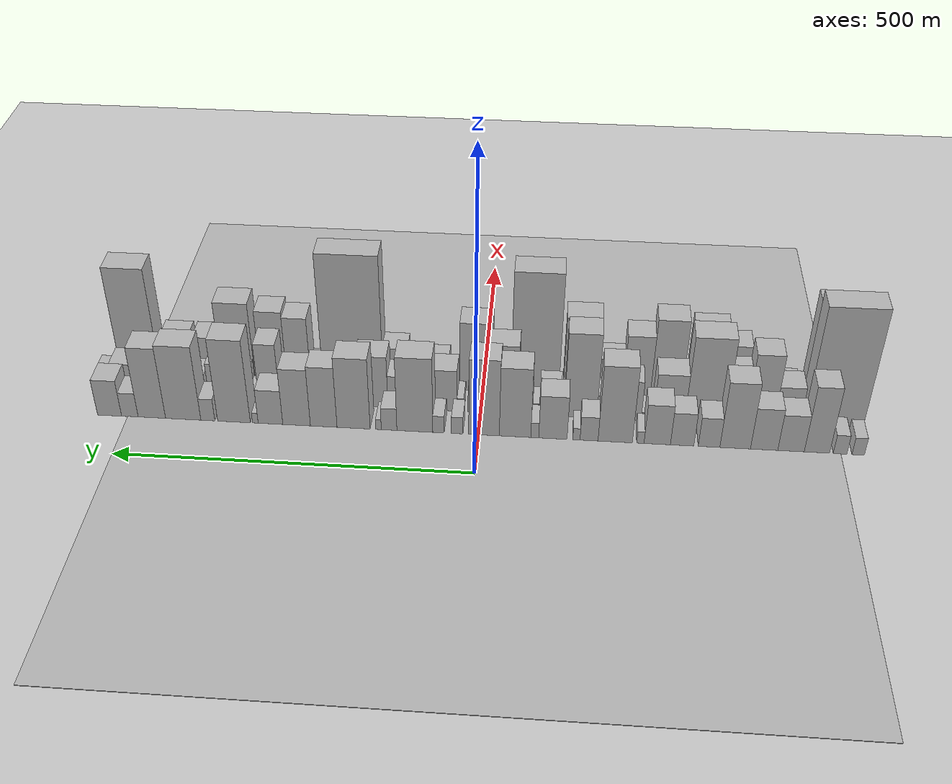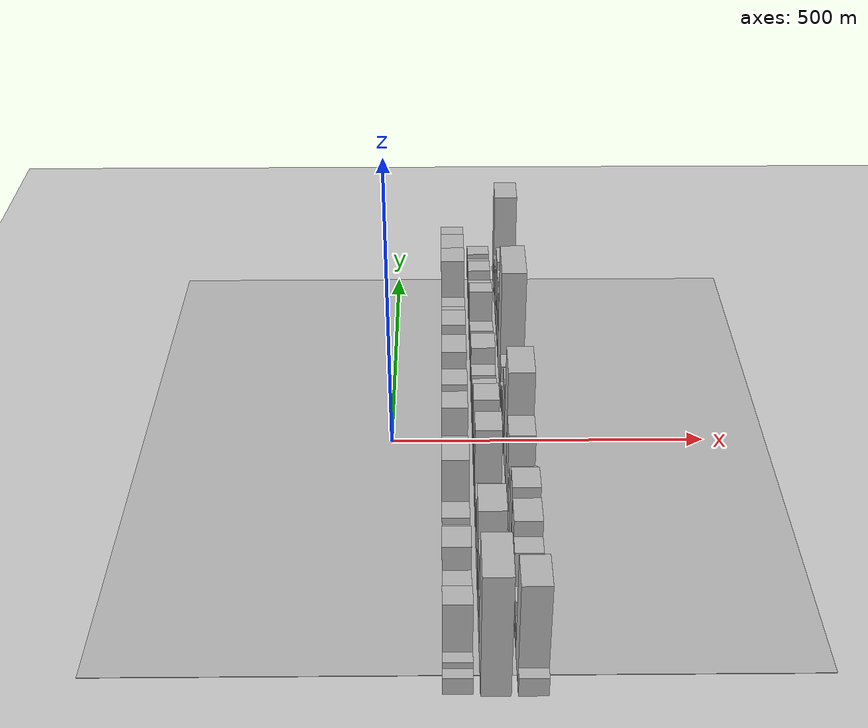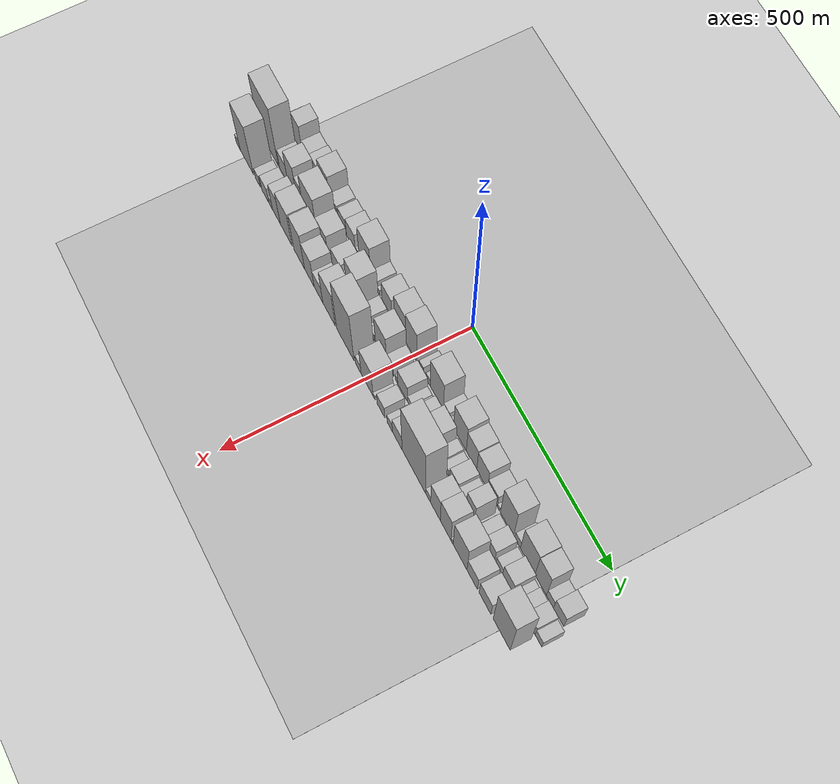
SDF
<?xml version="1.0" encoding="utf-8"?>

<sdf version="1.6">

   <world name="default">

      <gui fullscreen="0">

         <camera name="user_camera">

            <pose>-15 0 4.57585 0 0 0</pose>

            <view_controller>orbit</view_controller>

         </camera>

      </gui>

      <scene>

         <sky>

           <clouds>

             <speed>12</speed>

           </clouds>

         </sky>

         <ambient>0.4 0.4 0.4 1</ambient>

         <background>0.7 0.7 0.7 1</background>

         <shadows>1</shadows>

      </scene>

      <gravity>0 0 -9.8066</gravity>

      <magnetic_field>6e-06 2.3e-05 -4.2e-05</magnetic_field>

      <physics default="0" name="default_physics" type="ode">

         <ode>

            <solver>

               <type>quick</type>

               <iters>10</iters>

               <sor>1.0</sor>

               <use_dynamic_moi_rescaling>0</use_dynamic_moi_rescaling>

            </solver>

            <constraints>

               <cfm>0</cfm>

               <erp>0.2</erp>

               <contact_max_correcting_vel>100</contact_max_correcting_vel>

               <contact_surface_layer>0.001</contact_surface_layer>

            </constraints>

         </ode>

         <max_step_size>0.004</max_step_size>

         <real_time_factor>1</real_time_factor>

         <real_time_update_rate>250</real_time_update_rate>

      </physics>

      <light name="sun" type="directional">

         <cast_shadows>1</cast_shadows>

         <pose>0 0 10 0 0 0</pose>

         <diffuse>0.8 0.8 0.8 1</diffuse>

         <specular>0.2 0.2 0.2 1</specular>

         <attenuation>

            <range>1000</range>

            <constant>0.9</constant>

            <linear>0.01</linear>

            <quadratic>0.001</quadratic>

         </attenuation>

         <direction>-0.5 0.1 -0.9</direction>

      </light>

      <include>

         <name>ground_plane_1</name>

         <uri>model://HANNAS_ground_plane</uri>

         <pose>0 0 0  0 0 0</pose>

      </include>

      <include>

         <name>ground_plane_2</name>

         <uri>model://HANNAS_ground_plane</uri>

         <pose>100 0 0  0 0 0</pose>

      </include>

      <model name="building_1">

         <static>1</static>

         <pose frame="">100.0000 -523.5699 0 0.000000 0.000000 0.000000</pose>

         <link name="link">

            <pose frame="">0 0 15.00 0 0 0</pose>

            <collision name="collision">

               <geometry>

                  <box>

                     <size>40.0000 16.8602 30.0000</size>

                  </box>

               </geometry>

               <max_contacts>10</max_contacts>

               <surface>

                  <contact>

                     <ode/>

                  </contact>

                  <bounce/>

                  <friction>

                     <torsional>

                        <ode/>

                     </torsional>

                     <ode/>

                  </friction>

               </surface>

            </collision>

            <visual name="visual">

               <cast_shadows>0</cast_shadows>

               <geometry>

                  <box>

                     <size>40.0000 16.8602 30.0000</size>

                  </box>

               </geometry>

               <material>

                  <script>

                     <uri>model://HANNAS_wall/materials/scripts</uri>

                     <uri>model://HANNAS_wall/materials/textures</uri>

                     <name>vrc/HANNAS_wall</name>

                  </script>

               </material>

            </visual>

            <self_collide>0</self_collide>

            <enable_wind>0</enable_wind>

            <kinematic>0</kinematic>

         </link>

      </model>

      <model name="building_2">

         <static>1</static>

         <pose frame="">100.0000 -498.9160 0 0.000000 0.000000 0.000000</pose>

         <link name="link">

            <pose frame="">0 0 16.50 0 0 0</pose>

            <collision name="collision">

               <geometry>

                  <box>

                     <size>40.0000 18.4478 33.0000</size>

                  </box>

               </geometry>

               <max_contacts>10</max_contacts>

               <surface>

                  <contact>

                     <ode/>

                  </contact>

                  <bounce/>

                  <friction>

                     <torsional>

                        <ode/>

                     </torsional>

                     <ode/>

                  </friction>

               </surface>

            </collision>

            <visual name="visual">

               <cast_shadows>0</cast_shadows>

               <geometry>

                  <box>

                     <size>40.0000 18.4478 33.0000</size>

                  </box>

               </geometry>

               <material>

                  <script>

                     <uri>model://HANNAS_wall/materials/scripts</uri>

                     <uri>model://HANNAS_wall/materials/textures</uri>

                     <name>vrc/HANNAS_wall</name>

                  </script>

               </material>

            </visual>

            <self_collide>0</self_collide>

            <enable_wind>0</enable_wind>

            <kinematic>0</kinematic>

         </link>

      </model>

      <model name="building_3">

         <static>1</static>

         <pose frame="">100.0000 -467.4793 0 0.000000 0.000000 0.000000</pose>

         <link name="link">

            <pose frame="">0 0 57.00 0 0 0</pose>

            <collision name="collision">

               <geometry>

                  <box>

                     <size>40.0000 34.4256 114.0000</size>

                  </box>

               </geometry>

               <max_contacts>10</max_contacts>

               <surface>

                  <contact>

                     <ode/>

                  </contact>

                  <bounce/>

                  <friction>

                     <torsional>

                        <ode/>

                     </torsional>

                     <ode/>

                  </friction>

               </surface>

            </collision>

            <visual name="visual">

               <cast_shadows>0</cast_shadows>

               <geometry>

                  <box>

                     <size>40.0000 34.4256 114.0000</size>

                  </box>

               </geometry>

               <material>

                  <script>

                     <uri>model://HANNAS_wall/materials/scripts</uri>

                     <uri>model://HANNAS_wall/materials/textures</uri>

                     <name>vrc/HANNAS_wall</name>

                  </script>

               </material>

            </visual>

            <self_collide>0</self_collide>

            <enable_wind>0</enable_wind>

            <kinematic>0</kinematic>

         </link>

      </model>

      <model name="building_4">

         <static>1</static>

         <pose frame="">100.0000 -432.1780 0 0.000000 0.000000 0.000000</pose>

         <link name="link">

            <pose frame="">0 0 31.50 0 0 0</pose>

            <collision name="collision">

               <geometry>

                  <box>

                     <size>40.0000 36.1769 63.0000</size>

                  </box>

               </geometry>

               <max_contacts>10</max_contacts>

               <surface>

                  <contact>

                     <ode/>

                  </contact>

                  <bounce/>

                  <friction>

                     <torsional>

                        <ode/>

                     </torsional>

                     <ode/>

                  </friction>

               </surface>

            </collision>

            <visual name="visual">

               <cast_shadows>0</cast_shadows>

               <geometry>

                  <box>

                     <size>40.0000 36.1769 63.0000</size>

                  </box>

               </geometry>

               <material>

                  <script>

                     <uri>model://HANNAS_wall/materials/scripts</uri>

                     <uri>model://HANNAS_wall/materials/textures</uri>

                     <name>vrc/HANNAS_wall</name>

                  </script>

               </material>

            </visual>

            <self_collide>0</self_collide>

            <enable_wind>0</enable_wind>

            <kinematic>0</kinematic>

         </link>

      </model>

      <model name="building_5">

         <static>1</static>

         <pose frame="">100.0000 -395.4459 0 0.000000 0.000000 0.000000</pose>

         <link name="link">

            <pose frame="">0 0 36.00 0 0 0</pose>

            <collision name="collision">

               <geometry>

                  <box>

                     <size>40.0000 37.2872 72.0000</size>

                  </box>

               </geometry>

               <max_contacts>10</max_contacts>

               <surface>

                  <contact>

                     <ode/>

                  </contact>

                  <bounce/>

                  <friction>

                     <torsional>

                        <ode/>

                     </torsional>

                     <ode/>

                  </friction>

               </surface>

            </collision>

            <visual name="visual">

               <cast_shadows>0</cast_shadows>

               <geometry>

                  <box>

                     <size>40.0000 37.2872 72.0000</size>

                  </box>

               </geometry>

               <material>

                  <script>

                     <uri>model://HANNAS_wall/materials/scripts</uri>

                     <uri>model://HANNAS_wall/materials/textures</uri>

                     <name>vrc/HANNAS_wall</name>

                  </script>

               </material>

            </visual>

            <self_collide>0</self_collide>

            <enable_wind>0</enable_wind>

            <kinematic>0</kinematic>

         </link>

      </model>

      <model name="building_6">

         <static>1</static>

         <pose frame="">100.0000 -355.8213 0 0.000000 0.000000 0.000000</pose>

         <link name="link">

            <pose frame="">0 0 57.00 0 0 0</pose>

            <collision name="collision">

               <geometry>

                  <box>

                     <size>40.0000 41.9619 114.0000</size>

                  </box>

               </geometry>

               <max_contacts>10</max_contacts>

               <surface>

                  <contact>

                     <ode/>

                  </contact>

                  <bounce/>

                  <friction>

                     <torsional>

                        <ode/>

                     </torsional>

                     <ode/>

                  </friction>

               </surface>

            </collision>

            <visual name="visual">

               <cast_shadows>0</cast_shadows>

               <geometry>

                  <box>

                     <size>40.0000 41.9619 114.0000</size>

                  </box>

               </geometry>

               <material>

                  <script>

                     <uri>model://HANNAS_wall/materials/scripts</uri>

                     <uri>model://HANNAS_wall/materials/textures</uri>

                     <name>vrc/HANNAS_wall</name>

                  </script>

               </material>

            </visual>

            <self_collide>0</self_collide>

            <enable_wind>0</enable_wind>

            <kinematic>0</kinematic>

         </link>

      </model>

      <model name="building_7">

         <static>1</static>

         <pose frame="">100.0000 -319.9900 0 0.000000 0.000000 0.000000</pose>

         <link name="link">

            <pose frame="">0 0 25.50 0 0 0</pose>

            <collision name="collision">

               <geometry>

                  <box>

                     <size>40.0000 29.7007 51.0000</size>

                  </box>

               </geometry>

               <max_contacts>10</max_contacts>

               <surface>

                  <contact>

                     <ode/>

                  </contact>

                  <bounce/>

                  <friction>

                     <torsional>

                        <ode/>

                     </torsional>

                     <ode/>

                  </friction>

               </surface>

            </collision>

            <visual name="visual">

               <cast_shadows>0</cast_shadows>

               <geometry>

                  <box>

                     <size>40.0000 29.7007 51.0000</size>

                  </box>

               </geometry>

               <material>

                  <script>

                     <uri>model://HANNAS_wall/materials/scripts</uri>

                     <uri>model://HANNAS_wall/materials/textures</uri>

                     <name>vrc/HANNAS_wall</name>

                  </script>

               </material>

            </visual>

            <self_collide>0</self_collide>

            <enable_wind>0</enable_wind>

            <kinematic>0</kinematic>

         </link>

      </model>

      <model name="building_8">

         <static>1</static>

         <pose frame="">100.0000 -283.0301 0 0.000000 0.000000 0.000000</pose>

         <link name="link">

            <pose frame="">0 0 28.50 0 0 0</pose>

            <collision name="collision">

               <geometry>

                  <box>

                     <size>40.0000 32.2191 57.0000</size>

                  </box>

               </geometry>

               <max_contacts>10</max_contacts>

               <surface>

                  <contact>

                     <ode/>

                  </contact>

                  <bounce/>

                  <friction>

                     <torsional>

                        <ode/>

                     </torsional>

                     <ode/>

                  </friction>

               </surface>

            </collision>

            <visual name="visual">

               <cast_shadows>0</cast_shadows>

               <geometry>

                  <box>

                     <size>40.0000 32.2191 57.0000</size>

                  </box>

               </geometry>

               <material>

                  <script>

                     <uri>model://HANNAS_wall/materials/scripts</uri>

                     <uri>model://HANNAS_wall/materials/textures</uri>

                     <name>vrc/HANNAS_wall</name>

                  </script>

               </material>

            </visual>

            <self_collide>0</self_collide>

            <enable_wind>0</enable_wind>

            <kinematic>0</kinematic>

         </link>

      </model>

      <model name="building_9">

         <static>1</static>

         <pose frame="">100.0000 -248.7241 0 0.000000 0.000000 0.000000</pose>

         <link name="link">

            <pose frame="">0 0 34.50 0 0 0</pose>

            <collision name="collision">

               <geometry>

                  <box>

                     <size>40.0000 36.3929 69.0000</size>

                  </box>

               </geometry>

               <max_contacts>10</max_contacts>

               <surface>

                  <contact>

                     <ode/>

                  </contact>

                  <bounce/>

                  <friction>

                     <torsional>

                        <ode/>

                     </torsional>

                     <ode/>

                  </friction>

               </surface>

            </collision>

            <visual name="visual">

               <cast_shadows>0</cast_shadows>

               <geometry>

                  <box>

                     <size>40.0000 36.3929 69.0000</size>

                  </box>

               </geometry>

               <material>

                  <script>

                     <uri>model://HANNAS_wall/materials/scripts</uri>

                     <uri>model://HANNAS_wall/materials/textures</uri>

                     <name>vrc/HANNAS_wall</name>

                  </script>

               </material>

            </visual>

            <self_collide>0</self_collide>

            <enable_wind>0</enable_wind>

            <kinematic>0</kinematic>

         </link>

      </model>

      <model name="building_10">

         <static>1</static>

         <pose frame="">100.0000 -225.4781 0 0.000000 0.000000 0.000000</pose>

         <link name="link">

            <pose frame="">0 0 10.50 0 0 0</pose>

            <collision name="collision">

               <geometry>

                  <box>

                     <size>40.0000 10.0991 21.0000</size>

                  </box>

               </geometry>

               <max_contacts>10</max_contacts>

               <surface>

                  <contact>

                     <ode/>

                  </contact>

                  <bounce/>

                  <friction>

                     <torsional>

                        <ode/>

                     </torsional>

                     <ode/>

                  </friction>

               </surface>

            </collision>

            <visual name="visual">

               <cast_shadows>0</cast_shadows>

               <geometry>

                  <box>

                     <size>40.0000 10.0991 21.0000</size>

                  </box>

               </geometry>

               <material>

                  <script>

                     <uri>model://HANNAS_wall/materials/scripts</uri>

                     <uri>model://HANNAS_wall/materials/textures</uri>

                     <name>vrc/HANNAS_wall</name>

                  </script>

               </material>

            </visual>

            <self_collide>0</self_collide>

            <enable_wind>0</enable_wind>

            <kinematic>0</kinematic>

         </link>

      </model>

      <model name="building_11">

         <static>1</static>

         <pose frame="">100.0000 -190.6155 0 0.000000 0.000000 0.000000</pose>

         <link name="link">

            <pose frame="">0 0 66.00 0 0 0</pose>

            <collision name="collision">

               <geometry>

                  <box>

                     <size>40.0000 47.6261 132.0000</size>

                  </box>

               </geometry>

               <max_contacts>10</max_contacts>

               <surface>

                  <contact>

                     <ode/>

                  </contact>

                  <bounce/>

                  <friction>

                     <torsional>

                        <ode/>

                     </torsional>

                     <ode/>

                  </friction>

               </surface>

            </collision>

            <visual name="visual">

               <cast_shadows>0</cast_shadows>

               <geometry>

                  <box>

                     <size>40.0000 47.6261 132.0000</size>

                  </box>

               </geometry>

               <material>

                  <script>

                     <uri>model://HANNAS_wall/materials/scripts</uri>

                     <uri>model://HANNAS_wall/materials/textures</uri>

                     <name>vrc/HANNAS_wall</name>

                  </script>

               </material>

            </visual>

            <self_collide>0</self_collide>

            <enable_wind>0</enable_wind>

            <kinematic>0</kinematic>

         </link>

      </model>

      <model name="building_12">

         <static>1</static>

         <pose frame="">100.0000 -154.3334 0 0.000000 0.000000 0.000000</pose>

         <link name="link">

            <pose frame="">0 0 21.00 0 0 0</pose>

            <collision name="collision">

               <geometry>

                  <box>

                     <size>40.0000 24.9380 42.0000</size>

                  </box>

               </geometry>

               <max_contacts>10</max_contacts>

               <surface>

                  <contact>

                     <ode/>

                  </contact>

                  <bounce/>

                  <friction>

                     <torsional>

                        <ode/>

                     </torsional>

                     <ode/>

                  </friction>

               </surface>

            </collision>

            <visual name="visual">

               <cast_shadows>0</cast_shadows>

               <geometry>

                  <box>

                     <size>40.0000 24.9380 42.0000</size>

                  </box>

               </geometry>

               <material>

                  <script>

                     <uri>model://HANNAS_wall/materials/scripts</uri>

                     <uri>model://HANNAS_wall/materials/textures</uri>

                     <name>vrc/HANNAS_wall</name>

                  </script>

               </material>

            </visual>

            <self_collide>0</self_collide>

            <enable_wind>0</enable_wind>

            <kinematic>0</kinematic>

         </link>

      </model>

      <model name="building_13">

         <static>1</static>

         <pose frame="">100.0000 -136.8258 0 0.000000 0.000000 0.000000</pose>

         <link name="link">

            <pose frame="">0 0 10.50 0 0 0</pose>

            <collision name="collision">

               <geometry>

                  <box>

                     <size>40.0000 10.0771 21.0000</size>

                  </box>

               </geometry>

               <max_contacts>10</max_contacts>

               <surface>

                  <contact>

                     <ode/>

                  </contact>

                  <bounce/>

                  <friction>

                     <torsional>

                        <ode/>

                     </torsional>

                     <ode/>

                  </friction>

               </surface>

            </collision>

            <visual name="visual">

               <cast_shadows>0</cast_shadows>

               <geometry>

                  <box>

                     <size>40.0000 10.0771 21.0000</size>

                  </box>

               </geometry>

               <material>

                  <script>

                     <uri>model://HANNAS_wall/materials/scripts</uri>

                     <uri>model://HANNAS_wall/materials/textures</uri>

                     <name>vrc/HANNAS_wall</name>

                  </script>

               </material>

            </visual>

            <self_collide>0</self_collide>

            <enable_wind>0</enable_wind>

            <kinematic>0</kinematic>

         </link>

      </model>

      <model name="building_14">

         <static>1</static>

         <pose frame="">100.0000 -104.0365 0 0.000000 0.000000 0.000000</pose>

         <link name="link">

            <pose frame="">0 0 37.50 0 0 0</pose>

            <collision name="collision">

               <geometry>

                  <box>

                     <size>40.0000 39.5016 75.0000</size>

                  </box>

               </geometry>

               <max_contacts>10</max_contacts>

               <surface>

                  <contact>

                     <ode/>

                  </contact>

                  <bounce/>

                  <friction>

                     <torsional>

                        <ode/>

                     </torsional>

                     <ode/>

                  </friction>

               </surface>

            </collision>

            <visual name="visual">

               <cast_shadows>0</cast_shadows>

               <geometry>

                  <box>

                     <size>40.0000 39.5016 75.0000</size>

                  </box>

               </geometry>

               <material>

                  <script>

                     <uri>model://HANNAS_wall/materials/scripts</uri>

                     <uri>model://HANNAS_wall/materials/textures</uri>

                     <name>vrc/HANNAS_wall</name>

                  </script>

               </material>

            </visual>

            <self_collide>0</self_collide>

            <enable_wind>0</enable_wind>

            <kinematic>0</kinematic>

         </link>

      </model>

      <model name="building_15">

         <static>1</static>

         <pose frame="">100.0000 -78.7657 0 0.000000 0.000000 0.000000</pose>

         <link name="link">

            <pose frame="">0 0 13.50 0 0 0</pose>

            <collision name="collision">

               <geometry>

                  <box>

                     <size>40.0000 11.0400 27.0000</size>

                  </box>

               </geometry>

               <max_contacts>10</max_contacts>

               <surface>

                  <contact>

                     <ode/>

                  </contact>

                  <bounce/>

                  <friction>

                     <torsional>

                        <ode/>

                     </torsional>

                     <ode/>

                  </friction>

               </surface>

            </collision>

            <visual name="visual">

               <cast_shadows>0</cast_shadows>

               <geometry>

                  <box>

                     <size>40.0000 11.0400 27.0000</size>

                  </box>

               </geometry>

               <material>

                  <script>

                     <uri>model://HANNAS_wall/materials/scripts</uri>

                     <uri>model://HANNAS_wall/materials/textures</uri>

                     <name>vrc/HANNAS_wall</name>

                  </script>

               </material>

            </visual>

            <self_collide>0</self_collide>

            <enable_wind>0</enable_wind>

            <kinematic>0</kinematic>

         </link>

      </model>

      <model name="building_16">

         <static>1</static>

         <pose frame="">100.0000 -51.2539 0 0.000000 0.000000 0.000000</pose>

         <link name="link">

            <pose frame="">0 0 60.00 0 0 0</pose>

            <collision name="collision">

               <geometry>

                  <box>

                     <size>40.0000 43.9836 120.0000</size>

                  </box>

               </geometry>

               <max_contacts>10</max_contacts>

               <surface>

                  <contact>

                     <ode/>

                  </contact>

                  <bounce/>

                  <friction>

                     <torsional>

                        <ode/>

                     </torsional>

                     <ode/>

                  </friction>

               </surface>

            </collision>

            <visual name="visual">

               <cast_shadows>0</cast_shadows>

               <geometry>

                  <box>

                     <size>40.0000 43.9836 120.0000</size>

                  </box>

               </geometry>

               <material>

                  <script>

                     <uri>model://HANNAS_wall/materials/scripts</uri>

                     <uri>model://HANNAS_wall/materials/textures</uri>

                     <name>vrc/HANNAS_wall</name>

                  </script>

               </material>

            </visual>

            <self_collide>0</self_collide>

            <enable_wind>0</enable_wind>

            <kinematic>0</kinematic>

         </link>

      </model>

      <model name="building_17">

         <static>1</static>

         <pose frame="">100.0000 -7.7850 0 0.000000 0.000000 0.000000</pose>

         <link name="link">

            <pose frame="">0 0 66.00 0 0 0</pose>

            <collision name="collision">

               <geometry>

                  <box>

                     <size>40.0000 42.9540 132.0000</size>

                  </box>

               </geometry>

               <max_contacts>10</max_contacts>

               <surface>

                  <contact>

                     <ode/>

                  </contact>

                  <bounce/>

                  <friction>

                     <torsional>

                        <ode/>

                     </torsional>

                     <ode/>

                  </friction>

               </surface>

            </collision>

            <visual name="visual">

               <cast_shadows>0</cast_shadows>

               <geometry>

                  <box>

                     <size>40.0000 42.9540 132.0000</size>

                  </box>

               </geometry>

               <material>

                  <script>

                     <uri>model://HANNAS_wall/materials/scripts</uri>

                     <uri>model://HANNAS_wall/materials/textures</uri>

                     <name>vrc/HANNAS_wall</name>

                  </script>

               </material>

            </visual>

            <self_collide>0</self_collide>

            <enable_wind>0</enable_wind>

            <kinematic>0</kinematic>

         </link>

      </model>

      <model name="building_18">

         <static>1</static>

         <pose frame="">100.0000 29.8661 0 0.000000 0.000000 0.000000</pose>

         <link name="link">

            <pose frame="">0 0 15.00 0 0 0</pose>

            <collision name="collision">

               <geometry>

                  <box>

                     <size>40.0000 16.3483 30.0000</size>

                  </box>

               </geometry>

               <max_contacts>10</max_contacts>

               <surface>

                  <contact>

                     <ode/>

                  </contact>

                  <bounce/>

                  <friction>

                     <torsional>

                        <ode/>

                     </torsional>

                     <ode/>

                  </friction>

               </surface>

            </collision>

            <visual name="visual">

               <cast_shadows>0</cast_shadows>

               <geometry>

                  <box>

                     <size>40.0000 16.3483 30.0000</size>

                  </box>

               </geometry>

               <material>

                  <script>

                     <uri>model://HANNAS_wall/materials/scripts</uri>

                     <uri>model://HANNAS_wall/materials/textures</uri>

                     <name>vrc/HANNAS_wall</name>

                  </script>

               </material>

            </visual>

            <self_collide>0</self_collide>

            <enable_wind>0</enable_wind>

            <kinematic>0</kinematic>

         </link>

      </model>

      <model name="building_19">

         <static>1</static>

         <pose frame="">100.0000 56.0798 0 0.000000 0.000000 0.000000</pose>

         <link name="link">

            <pose frame="">0 0 15.00 0 0 0</pose>

            <collision name="collision">

               <geometry>

                  <box>

                     <size>40.0000 16.0791 30.0000</size>

                  </box>

               </geometry>

               <max_contacts>10</max_contacts>

               <surface>

                  <contact>

                     <ode/>

                  </contact>

                  <bounce/>

                  <friction>

                     <torsional>

                        <ode/>

                     </torsional>

                     <ode/>

                  </friction>

               </surface>

            </collision>

            <visual name="visual">

               <cast_shadows>0</cast_shadows>

               <geometry>

                  <box>

                     <size>40.0000 16.0791 30.0000</size>

                  </box>

               </geometry>

               <material>

                  <script>

                     <uri>model://HANNAS_wall/materials/scripts</uri>

                     <uri>model://HANNAS_wall/materials/textures</uri>

                     <name>vrc/HANNAS_wall</name>

                  </script>

               </material>

            </visual>

            <self_collide>0</self_collide>

            <enable_wind>0</enable_wind>

            <kinematic>0</kinematic>

         </link>

      </model>

      <model name="building_20">

         <static>1</static>

         <pose frame="">100.0000 89.4226 0 0.000000 0.000000 0.000000</pose>

         <link name="link">

            <pose frame="">0 0 64.50 0 0 0</pose>

            <collision name="collision">

               <geometry>

                  <box>

                     <size>40.0000 50.6065 129.0000</size>

                  </box>

               </geometry>

               <max_contacts>10</max_contacts>

               <surface>

                  <contact>

                     <ode/>

                  </contact>

                  <bounce/>

                  <friction>

                     <torsional>

                        <ode/>

                     </torsional>

                     <ode/>

                  </friction>

               </surface>

            </collision>

            <visual name="visual">

               <cast_shadows>0</cast_shadows>

               <geometry>

                  <box>

                     <size>40.0000 50.6065 129.0000</size>

                  </box>

               </geometry>

               <material>

                  <script>

                     <uri>model://HANNAS_wall/materials/scripts</uri>

                     <uri>model://HANNAS_wall/materials/textures</uri>

                     <name>vrc/HANNAS_wall</name>

                  </script>

               </material>

            </visual>

            <self_collide>0</self_collide>

            <enable_wind>0</enable_wind>

            <kinematic>0</kinematic>

         </link>

      </model>

      <model name="building_21">

         <static>1</static>

         <pose frame="">100.0000 125.7961 0 0.000000 0.000000 0.000000</pose>

         <link name="link">

            <pose frame="">0 0 19.50 0 0 0</pose>

            <collision name="collision">

               <geometry>

                  <box>

                     <size>40.0000 22.1406 39.0000</size>

                  </box>

               </geometry>

               <max_contacts>10</max_contacts>

               <surface>

                  <contact>

                     <ode/>

                  </contact>

                  <bounce/>

                  <friction>

                     <torsional>

                        <ode/>

                     </torsional>

                     <ode/>

                  </friction>

               </surface>

            </collision>

            <visual name="visual">

               <cast_shadows>0</cast_shadows>

               <geometry>

                  <box>

                     <size>40.0000 22.1406 39.0000</size>

                  </box>

               </geometry>

               <material>

                  <script>

                     <uri>model://HANNAS_wall/materials/scripts</uri>

                     <uri>model://HANNAS_wall/materials/textures</uri>

                     <name>vrc/HANNAS_wall</name>

                  </script>

               </material>

            </visual>

            <self_collide>0</self_collide>

            <enable_wind>0</enable_wind>

            <kinematic>0</kinematic>

         </link>

      </model>

      <model name="building_22">

         <static>1</static>

         <pose frame="">100.0000 140.7265 0 0.000000 0.000000 0.000000</pose>

         <link name="link">

            <pose frame="">0 0 9.00 0 0 0</pose>

            <collision name="collision">

               <geometry>

                  <box>

                     <size>40.0000 7.7201 18.0000</size>

                  </box>

               </geometry>

               <max_contacts>10</max_contacts>

               <surface>

                  <contact>

                     <ode/>

                  </contact>

                  <bounce/>

                  <friction>

                     <torsional>

                        <ode/>

                     </torsional>

                     <ode/>

                  </friction>

               </surface>

            </collision>

            <visual name="visual">

               <cast_shadows>0</cast_shadows>

               <geometry>

                  <box>

                     <size>40.0000 7.7201 18.0000</size>

                  </box>

               </geometry>

               <material>

                  <script>

                     <uri>model://HANNAS_wall/materials/scripts</uri>

                     <uri>model://HANNAS_wall/materials/textures</uri>

                     <name>vrc/HANNAS_wall</name>

                  </script>

               </material>

            </visual>

            <self_collide>0</self_collide>

            <enable_wind>0</enable_wind>

            <kinematic>0</kinematic>

         </link>

      </model>

      <model name="building_23">

         <static>1</static>

         <pose frame="">100.0000 176.0666 0 0.000000 0.000000 0.000000</pose>

         <link name="link">

            <pose frame="">0 0 61.50 0 0 0</pose>

            <collision name="collision">

               <geometry>

                  <box>

                     <size>40.0000 46.9602 123.0000</size>

                  </box>

               </geometry>

               <max_contacts>10</max_contacts>

               <surface>

                  <contact>

                     <ode/>

                  </contact>

                  <bounce/>

                  <friction>

                     <torsional>

                        <ode/>

                     </torsional>

                     <ode/>

                  </friction>

               </surface>

            </collision>

            <visual name="visual">

               <cast_shadows>0</cast_shadows>

               <geometry>

                  <box>

                     <size>40.0000 46.9602 123.0000</size>

                  </box>

               </geometry>

               <material>

                  <script>

                     <uri>model://HANNAS_wall/materials/scripts</uri>

                     <uri>model://HANNAS_wall/materials/textures</uri>

                     <name>vrc/HANNAS_wall</name>

                  </script>

               </material>

            </visual>

            <self_collide>0</self_collide>

            <enable_wind>0</enable_wind>

            <kinematic>0</kinematic>

         </link>

      </model>

      <model name="building_24">

         <static>1</static>

         <pose frame="">100.0000 218.4966 0 0.000000 0.000000 0.000000</pose>

         <link name="link">

            <pose frame="">0 0 52.50 0 0 0</pose>

            <collision name="collision">

               <geometry>

                  <box>

                     <size>40.0000 37.8998 105.0000</size>

                  </box>

               </geometry>

               <max_contacts>10</max_contacts>

               <surface>

                  <contact>

                     <ode/>

                  </contact>

                  <bounce/>

                  <friction>

                     <torsional>

                        <ode/>

                     </torsional>

                     <ode/>

                  </friction>

               </surface>

            </collision>

            <visual name="visual">

               <cast_shadows>0</cast_shadows>

               <geometry>

                  <box>

                     <size>40.0000 37.8998 105.0000</size>

                  </box>

               </geometry>

               <material>

                  <script>

                     <uri>model://HANNAS_wall/materials/scripts</uri>

                     <uri>model://HANNAS_wall/materials/textures</uri>

                     <name>vrc/HANNAS_wall</name>

                  </script>

               </material>

            </visual>

            <self_collide>0</self_collide>

            <enable_wind>0</enable_wind>

            <kinematic>0</kinematic>

         </link>

      </model>

      <model name="building_25">

         <static>1</static>

         <pose frame="">100.0000 257.1336 0 0.000000 0.000000 0.000000</pose>

         <link name="link">

            <pose frame="">0 0 49.50 0 0 0</pose>

            <collision name="collision">

               <geometry>

                  <box>

                     <size>40.0000 39.3741 99.0000</size>

                  </box>

               </geometry>

               <max_contacts>10</max_contacts>

               <surface>

                  <contact>

                     <ode/>

                  </contact>

                  <bounce/>

                  <friction>

                     <torsional>

                        <ode/>

                     </torsional>

                     <ode/>

                  </friction>

               </surface>

            </collision>

            <visual name="visual">

               <cast_shadows>0</cast_shadows>

               <geometry>

                  <box>

                     <size>40.0000 39.3741 99.0000</size>

                  </box>

               </geometry>

               <material>

                  <script>

                     <uri>model://HANNAS_wall/materials/scripts</uri>

                     <uri>model://HANNAS_wall/materials/textures</uri>

                     <name>vrc/HANNAS_wall</name>

                  </script>

               </material>

            </visual>

            <self_collide>0</self_collide>

            <enable_wind>0</enable_wind>

            <kinematic>0</kinematic>

         </link>

      </model>

      <model name="building_26">

         <static>1</static>

         <pose frame="">100.0000 294.4762 0 0.000000 0.000000 0.000000</pose>

         <link name="link">

            <pose frame="">0 0 30.00 0 0 0</pose>

            <collision name="collision">

               <geometry>

                  <box>

                     <size>40.0000 35.3112 60.0000</size>

                  </box>

               </geometry>

               <max_contacts>10</max_contacts>

               <surface>

                  <contact>

                     <ode/>

                  </contact>

                  <bounce/>

                  <friction>

                     <torsional>

                        <ode/>

                     </torsional>

                     <ode/>

                  </friction>

               </surface>

            </collision>

            <visual name="visual">

               <cast_shadows>0</cast_shadows>

               <geometry>

                  <box>

                     <size>40.0000 35.3112 60.0000</size>

                  </box>

               </geometry>

               <material>

                  <script>

                     <uri>model://HANNAS_wall/materials/scripts</uri>

                     <uri>model://HANNAS_wall/materials/textures</uri>

                     <name>vrc/HANNAS_wall</name>

                  </script>

               </material>

            </visual>

            <self_collide>0</self_collide>

            <enable_wind>0</enable_wind>

            <kinematic>0</kinematic>

         </link>

      </model>

      <model name="building_27">

         <static>1</static>

         <pose frame="">100.0000 316.2050 0 0.000000 0.000000 0.000000</pose>

         <link name="link">

            <pose frame="">0 0 9.00 0 0 0</pose>

            <collision name="collision">

               <geometry>

                  <box>

                     <size>40.0000 8.1465 18.0000</size>

                  </box>

               </geometry>

               <max_contacts>10</max_contacts>

               <surface>

                  <contact>

                     <ode/>

                  </contact>

                  <bounce/>

                  <friction>

                     <torsional>

                        <ode/>

                     </torsional>

                     <ode/>

                  </friction>

               </surface>

            </collision>

            <visual name="visual">

               <cast_shadows>0</cast_shadows>

               <geometry>

                  <box>

                     <size>40.0000 8.1465 18.0000</size>

                  </box>

               </geometry>

               <material>

                  <script>

                     <uri>model://HANNAS_wall/materials/scripts</uri>

                     <uri>model://HANNAS_wall/materials/textures</uri>

                     <name>vrc/HANNAS_wall</name>

                  </script>

               </material>

            </visual>

            <self_collide>0</self_collide>

            <enable_wind>0</enable_wind>

            <kinematic>0</kinematic>

         </link>

      </model>

      <model name="building_28">

         <static>1</static>

         <pose frame="">100.0000 346.7484 0 0.000000 0.000000 0.000000</pose>

         <link name="link">

            <pose frame="">0 0 72.00 0 0 0</pose>

            <collision name="collision">

               <geometry>

                  <box>

                     <size>40.0000 46.9402 144.0000</size>

                  </box>

               </geometry>

               <max_contacts>10</max_contacts>

               <surface>

                  <contact>

                     <ode/>

                  </contact>

                  <bounce/>

                  <friction>

                     <torsional>

                        <ode/>

                     </torsional>

                     <ode/>

                  </friction>

               </surface>

            </collision>

            <visual name="visual">

               <cast_shadows>0</cast_shadows>

               <geometry>

                  <box>

                     <size>40.0000 46.9402 144.0000</size>

                  </box>

               </geometry>

               <material>

                  <script>

                     <uri>model://HANNAS_wall/materials/scripts</uri>

                     <uri>model://HANNAS_wall/materials/textures</uri>

                     <name>vrc/HANNAS_wall</name>

                  </script>

               </material>

            </visual>

            <self_collide>0</self_collide>

            <enable_wind>0</enable_wind>

            <kinematic>0</kinematic>

         </link>

      </model>

      <model name="building_29">

         <static>1</static>

         <pose frame="">100.0000 384.2798 0 0.000000 0.000000 0.000000</pose>

         <link name="link">

            <pose frame="">0 0 19.50 0 0 0</pose>

            <collision name="collision">

               <geometry>

                  <box>

                     <size>40.0000 20.1228 39.0000</size>

                  </box>

               </geometry>

               <max_contacts>10</max_contacts>

               <surface>

                  <contact>

                     <ode/>

                  </contact>

                  <bounce/>

                  <friction>

                     <torsional>

                        <ode/>

                     </torsional>

                     <ode/>

                  </friction>

               </surface>

            </collision>

            <visual name="visual">

               <cast_shadows>0</cast_shadows>

               <geometry>

                  <box>

                     <size>40.0000 20.1228 39.0000</size>

                  </box>

               </geometry>

               <material>

                  <script>

                     <uri>model://HANNAS_wall/materials/scripts</uri>

                     <uri>model://HANNAS_wall/materials/textures</uri>

                     <name>vrc/HANNAS_wall</name>

                  </script>

               </material>

            </visual>

            <self_collide>0</self_collide>

            <enable_wind>0</enable_wind>

            <kinematic>0</kinematic>

         </link>

      </model>

      <model name="building_30">

         <static>1</static>

         <pose frame="">100.0000 419.7971 0 0.000000 0.000000 0.000000</pose>

         <link name="link">

            <pose frame="">0 0 64.50 0 0 0</pose>

            <collision name="collision">

               <geometry>

                  <box>

                     <size>40.0000 50.9118 129.0000</size>

                  </box>

               </geometry>

               <max_contacts>10</max_contacts>

               <surface>

                  <contact>

                     <ode/>

                  </contact>

                  <bounce/>

                  <friction>

                     <torsional>

                        <ode/>

                     </torsional>

                     <ode/>

                  </friction>

               </surface>

            </collision>

            <visual name="visual">

               <cast_shadows>0</cast_shadows>

               <geometry>

                  <box>

                     <size>40.0000 50.9118 129.0000</size>

                  </box>

               </geometry>

               <material>

                  <script>

                     <uri>model://HANNAS_wall/materials/scripts</uri>

                     <uri>model://HANNAS_wall/materials/textures</uri>

                     <name>vrc/HANNAS_wall</name>

                  </script>

               </material>

            </visual>

            <self_collide>0</self_collide>

            <enable_wind>0</enable_wind>

            <kinematic>0</kinematic>

         </link>

      </model>

      <model name="building_31">

         <static>1</static>

         <pose frame="">100.0000 465.1028 0 0.000000 0.000000 0.000000</pose>

         <link name="link">

            <pose frame="">0 0 61.50 0 0 0</pose>

            <collision name="collision">

               <geometry>

                  <box>

                     <size>40.0000 39.6996 123.0000</size>

                  </box>

               </geometry>

               <max_contacts>10</max_contacts>

               <surface>

                  <contact>

                     <ode/>

                  </contact>

                  <bounce/>

                  <friction>

                     <torsional>

                        <ode/>

                     </torsional>

                     <ode/>

                  </friction>

               </surface>

            </collision>

            <visual name="visual">

               <cast_shadows>0</cast_shadows>

               <geometry>

                  <box>

                     <size>40.0000 39.6996 123.0000</size>

                  </box>

               </geometry>

               <material>

                  <script>

                     <uri>model://HANNAS_wall/materials/scripts</uri>

                     <uri>model://HANNAS_wall/materials/textures</uri>

                     <name>vrc/HANNAS_wall</name>

                  </script>

               </material>

            </visual>

            <self_collide>0</self_collide>

            <enable_wind>0</enable_wind>

            <kinematic>0</kinematic>

         </link>

      </model>

      <model name="building_32">

         <static>1</static>

         <pose frame="">100.0000 496.9546 0 0.000000 0.000000 0.000000</pose>

         <link name="link">

            <pose frame="">0 0 21.00 0 0 0</pose>

            <collision name="collision">

               <geometry>

                  <box>

                     <size>40.0000 24.0039 42.0000</size>

                  </box>

               </geometry>

               <max_contacts>10</max_contacts>

               <surface>

                  <contact>

                     <ode/>

                  </contact>

                  <bounce/>

                  <friction>

                     <torsional>

                        <ode/>

                     </torsional>

                     <ode/>

                  </friction>

               </surface>

            </collision>

            <visual name="visual">

               <cast_shadows>0</cast_shadows>

               <geometry>

                  <box>

                     <size>40.0000 24.0039 42.0000</size>

                  </box>

               </geometry>

               <material>

                  <script>

                     <uri>model://HANNAS_wall/materials/scripts</uri>

                     <uri>model://HANNAS_wall/materials/textures</uri>

                     <name>vrc/HANNAS_wall</name>

                  </script>

               </material>

            </visual>

            <self_collide>0</self_collide>

            <enable_wind>0</enable_wind>

            <kinematic>0</kinematic>

         </link>

      </model>

      <model name="building_33">

         <static>1</static>

         <pose frame="">100.0000 526.4223 0 0.000000 0.000000 0.000000</pose>

         <link name="link">

            <pose frame="">0 0 31.50 0 0 0</pose>

            <collision name="collision">

               <geometry>

                  <box>

                     <size>40.0000 34.9316 63.0000</size>

                  </box>

               </geometry>

               <max_contacts>10</max_contacts>

               <surface>

                  <contact>

                     <ode/>

                  </contact>

                  <bounce/>

                  <friction>

                     <torsional>

                        <ode/>

                     </torsional>

                     <ode/>

                  </friction>

               </surface>

            </collision>

            <visual name="visual">

               <cast_shadows>0</cast_shadows>

               <geometry>

                  <box>

                     <size>40.0000 34.9316 63.0000</size>

                  </box>

               </geometry>

               <material>

                  <script>

                     <uri>model://HANNAS_wall/materials/scripts</uri>

                     <uri>model://HANNAS_wall/materials/textures</uri>

                     <name>vrc/HANNAS_wall</name>

                  </script>

               </material>

            </visual>

            <self_collide>0</self_collide>

            <enable_wind>0</enable_wind>

            <kinematic>0</kinematic>

         </link>

      </model>

      <model name="building_34">

         <static>1</static>

         <pose frame="">149.0000 -495.1231 0 0.000000 0.000000 0.000000</pose>

         <link name="link">

            <pose frame="">0 0 105.00 0 0 0</pose>

            <collision name="collision">

               <geometry>

                  <box>

                     <size>40.0000 81.7537 210.0000</size>

                  </box>

               </geometry>

               <max_contacts>10</max_contacts>

               <surface>

                  <contact>

                     <ode/>

                  </contact>

                  <bounce/>

                  <friction>

                     <torsional>

                        <ode/>

                     </torsional>

                     <ode/>

                  </friction>

               </surface>

            </collision>

            <visual name="visual">

               <cast_shadows>0</cast_shadows>

               <geometry>

                  <box>

                     <size>40.0000 81.7537 210.0000</size>

                  </box>

               </geometry>

               <material>

                  <script>

                     <uri>model://HANNAS_wall/materials/scripts</uri>

                     <uri>model://HANNAS_wall/materials/textures</uri>

                     <name>vrc/HANNAS_wall</name>

                  </script>

               </material>

            </visual>

            <self_collide>0</self_collide>

            <enable_wind>0</enable_wind>

            <kinematic>0</kinematic>

         </link>

      </model>

      <model name="building_35">

         <static>1</static>

         <pose frame="">149.0000 -431.0517 0 0.000000 0.000000 0.000000</pose>

         <link name="link">

            <pose frame="">0 0 36.00 0 0 0</pose>

            <collision name="collision">

               <geometry>

                  <box>

                     <size>40.0000 36.3891 72.0000</size>

                  </box>

               </geometry>

               <max_contacts>10</max_contacts>

               <surface>

                  <contact>

                     <ode/>

                  </contact>

                  <bounce/>

                  <friction>

                     <torsional>

                        <ode/>

                     </torsional>

                     <ode/>

                  </friction>

               </surface>

            </collision>

            <visual name="visual">

               <cast_shadows>0</cast_shadows>

               <geometry>

                  <box>

                     <size>40.0000 36.3891 72.0000</size>

                  </box>

               </geometry>

               <material>

                  <script>

                     <uri>model://HANNAS_wall/materials/scripts</uri>

                     <uri>model://HANNAS_wall/materials/textures</uri>

                     <name>vrc/HANNAS_wall</name>

                  </script>

               </material>

            </visual>

            <self_collide>0</self_collide>

            <enable_wind>0</enable_wind>

            <kinematic>0</kinematic>

         </link>

      </model>

      <model name="building_36">

         <static>1</static>

         <pose frame="">149.0000 -393.5010 0 0.000000 0.000000 0.000000</pose>

         <link name="link">

            <pose frame="">0 0 63.00 0 0 0</pose>

            <collision name="collision">

               <geometry>

                  <box>

                     <size>40.0000 38.7124 126.0000</size>

                  </box>

               </geometry>

               <max_contacts>10</max_contacts>

               <surface>

                  <contact>

                     <ode/>

                  </contact>

                  <bounce/>

                  <friction>

                     <torsional>

                        <ode/>

                     </torsional>

                     <ode/>

                  </friction>

               </surface>

            </collision>

            <visual name="visual">

               <cast_shadows>0</cast_shadows>

               <geometry>

                  <box>

                     <size>40.0000 38.7124 126.0000</size>

                  </box>

               </geometry>

               <material>

                  <script>

                     <uri>model://HANNAS_wall/materials/scripts</uri>

                     <uri>model://HANNAS_wall/materials/textures</uri>

                     <name>vrc/HANNAS_wall</name>

                  </script>

               </material>

            </visual>

            <self_collide>0</self_collide>

            <enable_wind>0</enable_wind>

            <kinematic>0</kinematic>

         </link>

      </model>

      <model name="building_37">

         <static>1</static>

         <pose frame="">149.0000 -359.9138 0 0.000000 0.000000 0.000000</pose>

         <link name="link">

            <pose frame="">0 0 46.50 0 0 0</pose>

            <collision name="collision">

               <geometry>

                  <box>

                     <size>40.0000 28.4620 93.0000</size>

                  </box>

               </geometry>

               <max_contacts>10</max_contacts>

               <surface>

                  <contact>

                     <ode/>

                  </contact>

                  <bounce/>

                  <friction>

                     <torsional>

                        <ode/>

                     </torsional>

                     <ode/>

                  </friction>

               </surface>

            </collision>

            <visual name="visual">

               <cast_shadows>0</cast_shadows>

               <geometry>

                  <box>

                     <size>40.0000 28.4620 93.0000</size>

                  </box>

               </geometry>

               <material>

                  <script>

                     <uri>model://HANNAS_wall/materials/scripts</uri>

                     <uri>model://HANNAS_wall/materials/textures</uri>

                     <name>vrc/HANNAS_wall</name>

                  </script>

               </material>

            </visual>

            <self_collide>0</self_collide>

            <enable_wind>0</enable_wind>

            <kinematic>0</kinematic>

         </link>

      </model>

      <model name="building_38">

         <static>1</static>

         <pose frame="">149.0000 -317.0915 0 0.000000 0.000000 0.000000</pose>

         <link name="link">

            <pose frame="">0 0 75.00 0 0 0</pose>

            <collision name="collision">

               <geometry>

                  <box>

                     <size>40.0000 57.1827 150.0000</size>

                  </box>

               </geometry>

               <max_contacts>10</max_contacts>

               <surface>

                  <contact>

                     <ode/>

                  </contact>

                  <bounce/>

                  <friction>

                     <torsional>

                        <ode/>

                     </torsional>

                     <ode/>

                  </friction>

               </surface>

            </collision>

            <visual name="visual">

               <cast_shadows>0</cast_shadows>

               <geometry>

                  <box>

                     <size>40.0000 57.1827 150.0000</size>

                  </box>

               </geometry>

               <material>

                  <script>

                     <uri>model://HANNAS_wall/materials/scripts</uri>

                     <uri>model://HANNAS_wall/materials/textures</uri>

                     <name>vrc/HANNAS_wall</name>

                  </script>

               </material>

            </visual>

            <self_collide>0</self_collide>

            <enable_wind>0</enable_wind>

            <kinematic>0</kinematic>

         </link>

      </model>

      <model name="building_39">

         <static>1</static>

         <pose frame="">149.0000 -266.5618 0 0.000000 0.000000 0.000000</pose>

         <link name="link">

            <pose frame="">0 0 42.00 0 0 0</pose>

            <collision name="collision">

               <geometry>

                  <box>

                     <size>40.0000 43.8767 84.0000</size>

                  </box>

               </geometry>

               <max_contacts>10</max_contacts>

               <surface>

                  <contact>

                     <ode/>

                  </contact>

                  <bounce/>

                  <friction>

                     <torsional>

                        <ode/>

                     </torsional>

                     <ode/>

                  </friction>

               </surface>

            </collision>

            <visual name="visual">

               <cast_shadows>0</cast_shadows>

               <geometry>

                  <box>

                     <size>40.0000 43.8767 84.0000</size>

                  </box>

               </geometry>

               <material>

                  <script>

                     <uri>model://HANNAS_wall/materials/scripts</uri>

                     <uri>model://HANNAS_wall/materials/textures</uri>

                     <name>vrc/HANNAS_wall</name>

                  </script>

               </material>

            </visual>

            <self_collide>0</self_collide>

            <enable_wind>0</enable_wind>

            <kinematic>0</kinematic>

         </link>

      </model>

      <model name="building_40">

         <static>1</static>

         <pose frame="">149.0000 -231.0600 0 0.000000 0.000000 0.000000</pose>

         <link name="link">

            <pose frame="">0 0 7.50 0 0 0</pose>

            <collision name="collision">

               <geometry>

                  <box>

                     <size>40.0000 7.1269 15.0000</size>

                  </box>

               </geometry>

               <max_contacts>10</max_contacts>

               <surface>

                  <contact>

                     <ode/>

                  </contact>

                  <bounce/>

                  <friction>

                     <torsional>

                        <ode/>

                     </torsional>

                     <ode/>

                  </friction>

               </surface>

            </collision>

            <visual name="visual">

               <cast_shadows>0</cast_shadows>

               <geometry>

                  <box>

                     <size>40.0000 7.1269 15.0000</size>

                  </box>

               </geometry>

               <material>

                  <script>

                     <uri>model://HANNAS_wall/materials/scripts</uri>

                     <uri>model://HANNAS_wall/materials/textures</uri>

                     <name>vrc/HANNAS_wall</name>

                  </script>

               </material>

            </visual>

            <self_collide>0</self_collide>

            <enable_wind>0</enable_wind>

            <kinematic>0</kinematic>

         </link>

      </model>

      <model name="building_41">

         <static>1</static>

         <pose frame="">149.0000 -208.1392 0 0.000000 0.000000 0.000000</pose>

         <link name="link">

            <pose frame="">0 0 34.50 0 0 0</pose>

            <collision name="collision">

               <geometry>

                  <box>

                     <size>40.0000 38.7147 69.0000</size>

                  </box>

               </geometry>

               <max_contacts>10</max_contacts>

               <surface>

                  <contact>

                     <ode/>

                  </contact>

                  <bounce/>

                  <friction>

                     <torsional>

                        <ode/>

                     </torsional>

                     <ode/>

                  </friction>

               </surface>

            </collision>

            <visual name="visual">

               <cast_shadows>0</cast_shadows>

               <geometry>

                  <box>

                     <size>40.0000 38.7147 69.0000</size>

                  </box>

               </geometry>

               <material>

                  <script>

                     <uri>model://HANNAS_wall/materials/scripts</uri>

                     <uri>model://HANNAS_wall/materials/textures</uri>

                     <name>vrc/HANNAS_wall</name>

                  </script>

               </material>

            </visual>

            <self_collide>0</self_collide>

            <enable_wind>0</enable_wind>

            <kinematic>0</kinematic>

         </link>

      </model>

      <model name="building_42">

         <static>1</static>

         <pose frame="">149.0000 -176.8376 0 0.000000 0.000000 0.000000</pose>

         <link name="link">

            <pose frame="">0 0 21.00 0 0 0</pose>

            <collision name="collision">

               <geometry>

                  <box>

                     <size>40.0000 23.8886 42.0000</size>

                  </box>

               </geometry>

               <max_contacts>10</max_contacts>

               <surface>

                  <contact>

                     <ode/>

                  </contact>

                  <bounce/>

                  <friction>

                     <torsional>

                        <ode/>

                     </torsional>

                     <ode/>

                  </friction>

               </surface>

            </collision>

            <visual name="visual">

               <cast_shadows>0</cast_shadows>

               <geometry>

                  <box>

                     <size>40.0000 23.8886 42.0000</size>

                  </box>

               </geometry>

               <material>

                  <script>

                     <uri>model://HANNAS_wall/materials/scripts</uri>

                     <uri>model://HANNAS_wall/materials/textures</uri>

                     <name>vrc/HANNAS_wall</name>

                  </script>

               </material>

            </visual>

            <self_collide>0</self_collide>

            <enable_wind>0</enable_wind>

            <kinematic>0</kinematic>

         </link>

      </model>

      <model name="building_43">

         <static>1</static>

         <pose frame="">149.0000 -141.6189 0 0.000000 0.000000 0.000000</pose>

         <link name="link">

            <pose frame="">0 0 73.50 0 0 0</pose>

            <collision name="collision">

               <geometry>

                  <box>

                     <size>40.0000 46.5488 147.0000</size>

                  </box>

               </geometry>

               <max_contacts>10</max_contacts>

               <surface>

                  <contact>

                     <ode/>

                  </contact>

                  <bounce/>

                  <friction>

                     <torsional>

                        <ode/>

                     </torsional>

                     <ode/>

                  </friction>

               </surface>

            </collision>

            <visual name="visual">

               <cast_shadows>0</cast_shadows>

               <geometry>

                  <box>

                     <size>40.0000 46.5488 147.0000</size>

                  </box>

               </geometry>

               <material>

                  <script>

                     <uri>model://HANNAS_wall/materials/scripts</uri>

                     <uri>model://HANNAS_wall/materials/textures</uri>

                     <name>vrc/HANNAS_wall</name>

                  </script>

               </material>

            </visual>

            <self_collide>0</self_collide>

            <enable_wind>0</enable_wind>

            <kinematic>0</kinematic>

         </link>

      </model>

      <model name="building_44">

         <static>1</static>

         <pose frame="">149.0000 -98.3548 0 0.000000 0.000000 0.000000</pose>

         <link name="link">

            <pose frame="">0 0 25.50 0 0 0</pose>

            <collision name="collision">

               <geometry>

                  <box>

                     <size>40.0000 29.9796 51.0000</size>

                  </box>

               </geometry>

               <max_contacts>10</max_contacts>

               <surface>

                  <contact>

                     <ode/>

                  </contact>

                  <bounce/>

                  <friction>

                     <torsional>

                        <ode/>

                     </torsional>

                     <ode/>

                  </friction>

               </surface>

            </collision>

            <visual name="visual">

               <cast_shadows>0</cast_shadows>

               <geometry>

                  <box>

                     <size>40.0000 29.9796 51.0000</size>

                  </box>

               </geometry>

               <material>

                  <script>

                     <uri>model://HANNAS_wall/materials/scripts</uri>

                     <uri>model://HANNAS_wall/materials/textures</uri>

                     <name>vrc/HANNAS_wall</name>

                  </script>

               </material>

            </visual>

            <self_collide>0</self_collide>

            <enable_wind>0</enable_wind>

            <kinematic>0</kinematic>

         </link>

      </model>

      <model name="building_45">

         <static>1</static>

         <pose frame="">149.0000 -78.6305 0 0.000000 0.000000 0.000000</pose>

         <link name="link">

            <pose frame="">0 0 10.50 0 0 0</pose>

            <collision name="collision">

               <geometry>

                  <box>

                     <size>40.0000 9.4690 21.0000</size>

                  </box>

               </geometry>

               <max_contacts>10</max_contacts>

               <surface>

                  <contact>

                     <ode/>

                  </contact>

                  <bounce/>

                  <friction>

                     <torsional>

                        <ode/>

                     </torsional>

                     <ode/>

                  </friction>

               </surface>

            </collision>

            <visual name="visual">

               <cast_shadows>0</cast_shadows>

               <geometry>

                  <box>

                     <size>40.0000 9.4690 21.0000</size>

                  </box>

               </geometry>

               <material>

                  <script>

                     <uri>model://HANNAS_wall/materials/scripts</uri>

                     <uri>model://HANNAS_wall/materials/textures</uri>

                     <name>vrc/HANNAS_wall</name>

                  </script>

               </material>

            </visual>

            <self_collide>0</self_collide>

            <enable_wind>0</enable_wind>

            <kinematic>0</kinematic>

         </link>

      </model>

      <model name="building_46">

         <static>1</static>

         <pose frame="">149.0000 -65.3582 0 0.000000 0.000000 0.000000</pose>

         <link name="link">

            <pose frame="">0 0 15.00 0 0 0</pose>

            <collision name="collision">

               <geometry>

                  <box>

                     <size>40.0000 17.0755 30.0000</size>

                  </box>

               </geometry>

               <max_contacts>10</max_contacts>

               <surface>

                  <contact>

                     <ode/>

                  </contact>

                  <bounce/>

                  <friction>

                     <torsional>

                        <ode/>

                     </torsional>

                     <ode/>

                  </friction>

               </surface>

            </collision>

            <visual name="visual">

               <cast_shadows>0</cast_shadows>

               <geometry>

                  <box>

                     <size>40.0000 17.0755 30.0000</size>

                  </box>

               </geometry>

               <material>

                  <script>

                     <uri>model://HANNAS_wall/materials/scripts</uri>

                     <uri>model://HANNAS_wall/materials/textures</uri>

                     <name>vrc/HANNAS_wall</name>

                  </script>

               </material>

            </visual>

            <self_collide>0</self_collide>

            <enable_wind>0</enable_wind>

            <kinematic>0</kinematic>

         </link>

      </model>

      <model name="building_47">

         <static>1</static>

         <pose frame="">149.0000 -30.7471 0 0.000000 0.000000 0.000000</pose>

         <link name="link">

            <pose frame="">0 0 60.00 0 0 0</pose>

            <collision name="collision">

               <geometry>

                  <box>

                     <size>40.0000 44.1467 120.0000</size>

                  </box>

               </geometry>

               <max_contacts>10</max_contacts>

               <surface>

                  <contact>

                     <ode/>

                  </contact>

                  <bounce/>

                  <friction>

                     <torsional>

                        <ode/>

                     </torsional>

                     <ode/>

                  </friction>

               </surface>

            </collision>

            <visual name="visual">

               <cast_shadows>0</cast_shadows>

               <geometry>

                  <box>

                     <size>40.0000 44.1467 120.0000</size>

                  </box>

               </geometry>

               <material>

                  <script>

                     <uri>model://HANNAS_wall/materials/scripts</uri>

                     <uri>model://HANNAS_wall/materials/textures</uri>

                     <name>vrc/HANNAS_wall</name>

                  </script>

               </material>

            </visual>

            <self_collide>0</self_collide>

            <enable_wind>0</enable_wind>

            <kinematic>0</kinematic>

         </link>

      </model>

      <model name="building_48">

         <static>1</static>

         <pose frame="">149.0000 4.8125 0 0.000000 0.000000 0.000000</pose>

         <link name="link">

            <pose frame="">0 0 24.00 0 0 0</pose>

            <collision name="collision">

               <geometry>

                  <box>

                     <size>40.0000 26.9725 48.0000</size>

                  </box>

               </geometry>

               <max_contacts>10</max_contacts>

               <surface>

                  <contact>

                     <ode/>

                  </contact>

                  <bounce/>

                  <friction>

                     <torsional>

                        <ode/>

                     </torsional>

                     <ode/>

                  </friction>

               </surface>

            </collision>

            <visual name="visual">

               <cast_shadows>0</cast_shadows>

               <geometry>

                  <box>

                     <size>40.0000 26.9725 48.0000</size>

                  </box>

               </geometry>

               <material>

                  <script>

                     <uri>model://HANNAS_wall/materials/scripts</uri>

                     <uri>model://HANNAS_wall/materials/textures</uri>

                     <name>vrc/HANNAS_wall</name>

                  </script>

               </material>

            </visual>

            <self_collide>0</self_collide>

            <enable_wind>0</enable_wind>

            <kinematic>0</kinematic>

         </link>

      </model>

      <model name="building_49">

         <static>1</static>

         <pose frame="">149.0000 29.1907 0 0.000000 0.000000 0.000000</pose>

         <link name="link">

            <pose frame="">0 0 12.00 0 0 0</pose>

            <collision name="collision">

               <geometry>

                  <box>

                     <size>40.0000 9.7840 24.0000</size>

                  </box>

               </geometry>

               <max_contacts>10</max_contacts>

               <surface>

                  <contact>

                     <ode/>

                  </contact>

                  <bounce/>

                  <friction>

                     <torsional>

                        <ode/>

                     </torsional>

                     <ode/>

                  </friction>

               </surface>

            </collision>

            <visual name="visual">

               <cast_shadows>0</cast_shadows>

               <geometry>

                  <box>

                     <size>40.0000 9.7840 24.0000</size>

                  </box>

               </geometry>

               <material>

                  <script>

                     <uri>model://HANNAS_wall/materials/scripts</uri>

                     <uri>model://HANNAS_wall/materials/textures</uri>

                     <name>vrc/HANNAS_wall</name>

                  </script>

               </material>

            </visual>

            <self_collide>0</self_collide>

            <enable_wind>0</enable_wind>

            <kinematic>0</kinematic>

         </link>

      </model>

      <model name="building_50">

         <static>1</static>

         <pose frame="">149.0000 52.8915 0 0.000000 0.000000 0.000000</pose>

         <link name="link">

            <pose frame="">0 0 36.00 0 0 0</pose>

            <collision name="collision">

               <geometry>

                  <box>

                     <size>40.0000 37.6177 72.0000</size>

                  </box>

               </geometry>

               <max_contacts>10</max_contacts>

               <surface>

                  <contact>

                     <ode/>

                  </contact>

                  <bounce/>

                  <friction>

                     <torsional>

                        <ode/>

                     </torsional>

                     <ode/>

                  </friction>

               </surface>

            </collision>

            <visual name="visual">

               <cast_shadows>0</cast_shadows>

               <geometry>

                  <box>

                     <size>40.0000 37.6177 72.0000</size>

                  </box>

               </geometry>

               <material>

                  <script>

                     <uri>model://HANNAS_wall/materials/scripts</uri>

                     <uri>model://HANNAS_wall/materials/textures</uri>

                     <name>vrc/HANNAS_wall</name>

                  </script>

               </material>

            </visual>

            <self_collide>0</self_collide>

            <enable_wind>0</enable_wind>

            <kinematic>0</kinematic>

         </link>

      </model>

      <model name="building_51">

         <static>1</static>

         <pose frame="">149.0000 80.6054 0 0.000000 0.000000 0.000000</pose>

         <link name="link">

            <pose frame="">0 0 15.00 0 0 0</pose>

            <collision name="collision">

               <geometry>

                  <box>

                     <size>40.0000 17.8101 30.0000</size>

                  </box>

               </geometry>

               <max_contacts>10</max_contacts>

               <surface>

                  <contact>

                     <ode/>

                  </contact>

                  <bounce/>

                  <friction>

                     <torsional>

                        <ode/>

                     </torsional>

                     <ode/>

                  </friction>

               </surface>

            </collision>

            <visual name="visual">

               <cast_shadows>0</cast_shadows>

               <geometry>

                  <box>

                     <size>40.0000 17.8101 30.0000</size>

                  </box>

               </geometry>

               <material>

                  <script>

                     <uri>model://HANNAS_wall/materials/scripts</uri>

                     <uri>model://HANNAS_wall/materials/textures</uri>

                     <name>vrc/HANNAS_wall</name>

                  </script>

               </material>

            </visual>

            <self_collide>0</self_collide>

            <enable_wind>0</enable_wind>

            <kinematic>0</kinematic>

         </link>

      </model>

      <model name="building_52">

         <static>1</static>

         <pose frame="">149.0000 95.2533 0 0.000000 0.000000 0.000000</pose>

         <link name="link">

            <pose frame="">0 0 13.50 0 0 0</pose>

            <collision name="collision">

               <geometry>

                  <box>

                     <size>40.0000 11.4857 27.0000</size>

                  </box>

               </geometry>

               <max_contacts>10</max_contacts>

               <surface>

                  <contact>

                     <ode/>

                  </contact>

                  <bounce/>

                  <friction>

                     <torsional>

                        <ode/>

                     </torsional>

                     <ode/>

                  </friction>

               </surface>

            </collision>

            <visual name="visual">

               <cast_shadows>0</cast_shadows>

               <geometry>

                  <box>

                     <size>40.0000 11.4857 27.0000</size>

                  </box>

               </geometry>

               <material>

                  <script>

                     <uri>model://HANNAS_wall/materials/scripts</uri>

                     <uri>model://HANNAS_wall/materials/textures</uri>

                     <name>vrc/HANNAS_wall</name>

                  </script>

               </material>

            </visual>

            <self_collide>0</self_collide>

            <enable_wind>0</enable_wind>

            <kinematic>0</kinematic>

         </link>

      </model>

      <model name="building_53">

         <static>1</static>

         <pose frame="">149.0000 117.1469 0 0.000000 0.000000 0.000000</pose>

         <link name="link">

            <pose frame="">0 0 28.50 0 0 0</pose>

            <collision name="collision">

               <geometry>

                  <box>

                     <size>40.0000 32.3017 57.0000</size>

                  </box>

               </geometry>

               <max_contacts>10</max_contacts>

               <surface>

                  <contact>

                     <ode/>

                  </contact>

                  <bounce/>

                  <friction>

                     <torsional>

                        <ode/>

                     </torsional>

                     <ode/>

                  </friction>

               </surface>

            </collision>

            <visual name="visual">

               <cast_shadows>0</cast_shadows>

               <geometry>

                  <box>

                     <size>40.0000 32.3017 57.0000</size>

                  </box>

               </geometry>

               <material>

                  <script>

                     <uri>model://HANNAS_wall/materials/scripts</uri>

                     <uri>model://HANNAS_wall/materials/textures</uri>

                     <name>vrc/HANNAS_wall</name>

                  </script>

               </material>

            </visual>

            <self_collide>0</self_collide>

            <enable_wind>0</enable_wind>

            <kinematic>0</kinematic>

         </link>

      </model>

      <model name="building_54">

         <static>1</static>

         <pose frame="">149.0000 155.9006 0 0.000000 0.000000 0.000000</pose>

         <link name="link">

            <pose frame="">0 0 45.00 0 0 0</pose>

            <collision name="collision">

               <geometry>

                  <box>

                     <size>40.0000 45.2056 90.0000</size>

                  </box>

               </geometry>

               <max_contacts>10</max_contacts>

               <surface>

                  <contact>

                     <ode/>

                  </contact>

                  <bounce/>

                  <friction>

                     <torsional>

                        <ode/>

                     </torsional>

                     <ode/>

                  </friction>

               </surface>

            </collision>

            <visual name="visual">

               <cast_shadows>0</cast_shadows>

               <geometry>

                  <box>

                     <size>40.0000 45.2056 90.0000</size>

                  </box>

               </geometry>

               <material>

                  <script>

                     <uri>model://HANNAS_wall/materials/scripts</uri>

                     <uri>model://HANNAS_wall/materials/textures</uri>

                     <name>vrc/HANNAS_wall</name>

                  </script>

               </material>

            </visual>

            <self_collide>0</self_collide>

            <enable_wind>0</enable_wind>

            <kinematic>0</kinematic>

         </link>

      </model>

      <model name="building_55">

         <static>1</static>

         <pose frame="">149.0000 194.3009 0 0.000000 0.000000 0.000000</pose>

         <link name="link">

            <pose frame="">0 0 21.00 0 0 0</pose>

            <collision name="collision">

               <geometry>

                  <box>

                     <size>40.0000 23.5950 42.0000</size>

                  </box>

               </geometry>

               <max_contacts>10</max_contacts>

               <surface>

                  <contact>

                     <ode/>

                  </contact>

                  <bounce/>

                  <friction>

                     <torsional>

                        <ode/>

                     </torsional>

                     <ode/>

                  </friction>

               </surface>

            </collision>

            <visual name="visual">

               <cast_shadows>0</cast_shadows>

               <geometry>

                  <box>

                     <size>40.0000 23.5950 42.0000</size>

                  </box>

               </geometry>

               <material>

                  <script>

                     <uri>model://HANNAS_wall/materials/scripts</uri>

                     <uri>model://HANNAS_wall/materials/textures</uri>

                     <name>vrc/HANNAS_wall</name>

                  </script>

               </material>

            </visual>

            <self_collide>0</self_collide>

            <enable_wind>0</enable_wind>

            <kinematic>0</kinematic>

         </link>

      </model>

      <model name="building_56">

         <static>1</static>

         <pose frame="">149.0000 215.7939 0 0.000000 0.000000 0.000000</pose>

         <link name="link">

            <pose frame="">0 0 16.50 0 0 0</pose>

            <collision name="collision">

               <geometry>

                  <box>

                     <size>40.0000 19.3909 33.0000</size>

                  </box>

               </geometry>

               <max_contacts>10</max_contacts>

               <surface>

                  <contact>

                     <ode/>

                  </contact>

                  <bounce/>

                  <friction>

                     <torsional>

                        <ode/>

                     </torsional>

                     <ode/>

                  </friction>

               </surface>

            </collision>

            <visual name="visual">

               <cast_shadows>0</cast_shadows>

               <geometry>

                  <box>

                     <size>40.0000 19.3909 33.0000</size>

                  </box>

               </geometry>

               <material>

                  <script>

                     <uri>model://HANNAS_wall/materials/scripts</uri>

                     <uri>model://HANNAS_wall/materials/textures</uri>

                     <name>vrc/HANNAS_wall</name>

                  </script>

               </material>

            </visual>

            <self_collide>0</self_collide>

            <enable_wind>0</enable_wind>

            <kinematic>0</kinematic>

         </link>

      </model>

      <model name="building_57">

         <static>1</static>

         <pose frame="">149.0000 245.4726 0 0.000000 0.000000 0.000000</pose>

         <link name="link">

            <pose frame="">0 0 30.00 0 0 0</pose>

            <collision name="collision">

               <geometry>

                  <box>

                     <size>40.0000 31.9666 60.0000</size>

                  </box>

               </geometry>

               <max_contacts>10</max_contacts>

               <surface>

                  <contact>

                     <ode/>

                  </contact>

                  <bounce/>

                  <friction>

                     <torsional>

                        <ode/>

                     </torsional>

                     <ode/>

                  </friction>

               </surface>

            </collision>

            <visual name="visual">

               <cast_shadows>0</cast_shadows>

               <geometry>

                  <box>

                     <size>40.0000 31.9666 60.0000</size>

                  </box>

               </geometry>

               <material>

                  <script>

                     <uri>model://HANNAS_wall/materials/scripts</uri>

                     <uri>model://HANNAS_wall/materials/textures</uri>

                     <name>vrc/HANNAS_wall</name>

                  </script>

               </material>

            </visual>

            <self_collide>0</self_collide>

            <enable_wind>0</enable_wind>

            <kinematic>0</kinematic>

         </link>

      </model>

      <model name="building_58">

         <static>1</static>

         <pose frame="">149.0000 273.6602 0 0.000000 0.000000 0.000000</pose>

         <link name="link">

            <pose frame="">0 0 21.00 0 0 0</pose>

            <collision name="collision">

               <geometry>

                  <box>

                     <size>40.0000 24.4086 42.0000</size>

                  </box>

               </geometry>

               <max_contacts>10</max_contacts>

               <surface>

                  <contact>

                     <ode/>

                  </contact>

                  <bounce/>

                  <friction>

                     <torsional>

                        <ode/>

                     </torsional>

                     <ode/>

                  </friction>

               </surface>

            </collision>

            <visual name="visual">

               <cast_shadows>0</cast_shadows>

               <geometry>

                  <box>

                     <size>40.0000 24.4086 42.0000</size>

                  </box>

               </geometry>

               <material>

                  <script>

                     <uri>model://HANNAS_wall/materials/scripts</uri>

                     <uri>model://HANNAS_wall/materials/textures</uri>

                     <name>vrc/HANNAS_wall</name>

                  </script>

               </material>

            </visual>

            <self_collide>0</self_collide>

            <enable_wind>0</enable_wind>

            <kinematic>0</kinematic>

         </link>

      </model>

      <model name="building_59">

         <static>1</static>

         <pose frame="">149.0000 305.2462 0 0.000000 0.000000 0.000000</pose>

         <link name="link">

            <pose frame="">0 0 51.00 0 0 0</pose>

            <collision name="collision">

               <geometry>

                  <box>

                     <size>40.0000 30.7636 102.0000</size>

                  </box>

               </geometry>

               <max_contacts>10</max_contacts>

               <surface>

                  <contact>

                     <ode/>

                  </contact>

                  <bounce/>

                  <friction>

                     <torsional>

                        <ode/>

                     </torsional>

                     <ode/>

                  </friction>

               </surface>

            </collision>

            <visual name="visual">

               <cast_shadows>0</cast_shadows>

               <geometry>

                  <box>

                     <size>40.0000 30.7636 102.0000</size>

                  </box>

               </geometry>

               <material>

                  <script>

                     <uri>model://HANNAS_wall/materials/scripts</uri>

                     <uri>model://HANNAS_wall/materials/textures</uri>

                     <name>vrc/HANNAS_wall</name>

                  </script>

               </material>

            </visual>

            <self_collide>0</self_collide>

            <enable_wind>0</enable_wind>

            <kinematic>0</kinematic>

         </link>

      </model>

      <model name="building_60">

         <static>1</static>

         <pose frame="">149.0000 330.9121 0 0.000000 0.000000 0.000000</pose>

         <link name="link">

            <pose frame="">0 0 7.50 0 0 0</pose>

            <collision name="collision">

               <geometry>

                  <box>

                     <size>40.0000 6.5682 15.0000</size>

                  </box>

               </geometry>

               <max_contacts>10</max_contacts>

               <surface>

                  <contact>

                     <ode/>

                  </contact>

                  <bounce/>

                  <friction>

                     <torsional>

                        <ode/>

                     </torsional>

                     <ode/>

                  </friction>

               </surface>

            </collision>

            <visual name="visual">

               <cast_shadows>0</cast_shadows>

               <geometry>

                  <box>

                     <size>40.0000 6.5682 15.0000</size>

                  </box>

               </geometry>

               <material>

                  <script>

                     <uri>model://HANNAS_wall/materials/scripts</uri>

                     <uri>model://HANNAS_wall/materials/textures</uri>

                     <name>vrc/HANNAS_wall</name>

                  </script>

               </material>

            </visual>

            <self_collide>0</self_collide>

            <enable_wind>0</enable_wind>

            <kinematic>0</kinematic>

         </link>

      </model>

      <model name="building_61">

         <static>1</static>

         <pose frame="">149.0000 347.6319 0 0.000000 0.000000 0.000000</pose>

         <link name="link">

            <pose frame="">0 0 22.50 0 0 0</pose>

            <collision name="collision">

               <geometry>

                  <box>

                     <size>40.0000 26.8714 45.0000</size>

                  </box>

               </geometry>

               <max_contacts>10</max_contacts>

               <surface>

                  <contact>

                     <ode/>

                  </contact>

                  <bounce/>

                  <friction>

                     <torsional>

                        <ode/>

                     </torsional>

                     <ode/>

                  </friction>

               </surface>

            </collision>

            <visual name="visual">

               <cast_shadows>0</cast_shadows>

               <geometry>

                  <box>

                     <size>40.0000 26.8714 45.0000</size>

                  </box>

               </geometry>

               <material>

                  <script>

                     <uri>model://HANNAS_wall/materials/scripts</uri>

                     <uri>model://HANNAS_wall/materials/textures</uri>

                     <name>vrc/HANNAS_wall</name>

                  </script>

               </material>

            </visual>

            <self_collide>0</self_collide>

            <enable_wind>0</enable_wind>

            <kinematic>0</kinematic>

         </link>

      </model>

      <model name="building_62">

         <static>1</static>

         <pose frame="">149.0000 377.2126 0 0.000000 0.000000 0.000000</pose>

         <link name="link">

            <pose frame="">0 0 31.50 0 0 0</pose>

            <collision name="collision">

               <geometry>

                  <box>

                     <size>40.0000 32.2900 63.0000</size>

                  </box>

               </geometry>

               <max_contacts>10</max_contacts>

               <surface>

                  <contact>

                     <ode/>

                  </contact>

                  <bounce/>

                  <friction>

                     <torsional>

                        <ode/>

                     </torsional>

                     <ode/>

                  </friction>

               </surface>

            </collision>

            <visual name="visual">

               <cast_shadows>0</cast_shadows>

               <geometry>

                  <box>

                     <size>40.0000 32.2900 63.0000</size>

                  </box>

               </geometry>

               <material>

                  <script>

                     <uri>model://HANNAS_wall/materials/scripts</uri>

                     <uri>model://HANNAS_wall/materials/textures</uri>

                     <name>vrc/HANNAS_wall</name>

                  </script>

               </material>

            </visual>

            <self_collide>0</self_collide>

            <enable_wind>0</enable_wind>

            <kinematic>0</kinematic>

         </link>

      </model>

      <model name="building_63">

         <static>1</static>

         <pose frame="">149.0000 409.0577 0 0.000000 0.000000 0.000000</pose>

         <link name="link">

            <pose frame="">0 0 21.00 0 0 0</pose>

            <collision name="collision">

               <geometry>

                  <box>

                     <size>40.0000 23.4001 42.0000</size>

                  </box>

               </geometry>

               <max_contacts>10</max_contacts>

               <surface>

                  <contact>

                     <ode/>

                  </contact>

                  <bounce/>

                  <friction>

                     <torsional>

                        <ode/>

                     </torsional>

                     <ode/>

                  </friction>

               </surface>

            </collision>

            <visual name="visual">

               <cast_shadows>0</cast_shadows>

               <geometry>

                  <box>

                     <size>40.0000 23.4001 42.0000</size>

                  </box>

               </geometry>

               <material>

                  <script>

                     <uri>model://HANNAS_wall/materials/scripts</uri>

                     <uri>model://HANNAS_wall/materials/textures</uri>

                     <name>vrc/HANNAS_wall</name>

                  </script>

               </material>

            </visual>

            <self_collide>0</self_collide>

            <enable_wind>0</enable_wind>

            <kinematic>0</kinematic>

         </link>

      </model>

      <model name="building_64">

         <static>1</static>

         <pose frame="">149.0000 439.0651 0 0.000000 0.000000 0.000000</pose>

         <link name="link">

            <pose frame="">0 0 33.00 0 0 0</pose>

            <collision name="collision">

               <geometry>

                  <box>

                     <size>40.0000 36.6147 66.0000</size>

                  </box>

               </geometry>

               <max_contacts>10</max_contacts>

               <surface>

                  <contact>

                     <ode/>

                  </contact>

                  <bounce/>

                  <friction>

                     <torsional>

                        <ode/>

                     </torsional>

                     <ode/>

                  </friction>

               </surface>

            </collision>

            <visual name="visual">

               <cast_shadows>0</cast_shadows>

               <geometry>

                  <box>

                     <size>40.0000 36.6147 66.0000</size>

                  </box>

               </geometry>

               <material>

                  <script>

                     <uri>model://HANNAS_wall/materials/scripts</uri>

                     <uri>model://HANNAS_wall/materials/textures</uri>

                     <name>vrc/HANNAS_wall</name>

                  </script>

               </material>

            </visual>

            <self_collide>0</self_collide>

            <enable_wind>0</enable_wind>

            <kinematic>0</kinematic>

         </link>

      </model>

      <model name="building_65">

         <static>1</static>

         <pose frame="">149.0000 466.0553 0 0.000000 0.000000 0.000000</pose>

         <link name="link">

            <pose frame="">0 0 16.50 0 0 0</pose>

            <collision name="collision">

               <geometry>

                  <box>

                     <size>40.0000 17.3658 33.0000</size>

                  </box>

               </geometry>

               <max_contacts>10</max_contacts>

               <surface>

                  <contact>

                     <ode/>

                  </contact>

                  <bounce/>

                  <friction>

                     <torsional>

                        <ode/>

                     </torsional>

                     <ode/>

                  </friction>

               </surface>

            </collision>

            <visual name="visual">

               <cast_shadows>0</cast_shadows>

               <geometry>

                  <box>

                     <size>40.0000 17.3658 33.0000</size>

                  </box>

               </geometry>

               <material>

                  <script>

                     <uri>model://HANNAS_wall/materials/scripts</uri>

                     <uri>model://HANNAS_wall/materials/textures</uri>

                     <name>vrc/HANNAS_wall</name>

                  </script>

               </material>

            </visual>

            <self_collide>0</self_collide>

            <enable_wind>0</enable_wind>

            <kinematic>0</kinematic>

         </link>

      </model>

      <model name="building_66">

         <static>1</static>

         <pose frame="">149.0000 488.1993 0 0.000000 0.000000 0.000000</pose>

         <link name="link">

            <pose frame="">0 0 22.50 0 0 0</pose>

            <collision name="collision">

               <geometry>

                  <box>

                     <size>40.0000 26.9221 45.0000</size>

                  </box>

               </geometry>

               <max_contacts>10</max_contacts>

               <surface>

                  <contact>

                     <ode/>

                  </contact>

                  <bounce/>

                  <friction>

                     <torsional>

                        <ode/>

                     </torsional>

                     <ode/>

                  </friction>

               </surface>

            </collision>

            <visual name="visual">

               <cast_shadows>0</cast_shadows>

               <geometry>

                  <box>

                     <size>40.0000 26.9221 45.0000</size>

                  </box>

               </geometry>

               <material>

                  <script>

                     <uri>model://HANNAS_wall/materials/scripts</uri>

                     <uri>model://HANNAS_wall/materials/textures</uri>

                     <name>vrc/HANNAS_wall</name>

                  </script>

               </material>

            </visual>

            <self_collide>0</self_collide>

            <enable_wind>0</enable_wind>

            <kinematic>0</kinematic>

         </link>

      </model>

      <model name="building_67">

         <static>1</static>

         <pose frame="">149.0000 517.8214 0 0.000000 0.000000 0.000000</pose>

         <link name="link">

            <pose frame="">0 0 27.00 0 0 0</pose>

            <collision name="collision">

               <geometry>

                  <box>

                     <size>40.0000 32.3223 54.0000</size>

                  </box>

               </geometry>

               <max_contacts>10</max_contacts>

               <surface>

                  <contact>

                     <ode/>

                  </contact>

                  <bounce/>

                  <friction>

                     <torsional>

                        <ode/>

                     </torsional>

                     <ode/>

                  </friction>

               </surface>

            </collision>

            <visual name="visual">

               <cast_shadows>0</cast_shadows>

               <geometry>

                  <box>

                     <size>40.0000 32.3223 54.0000</size>

                  </box>

               </geometry>

               <material>

                  <script>

                     <uri>model://HANNAS_wall/materials/scripts</uri>

                     <uri>model://HANNAS_wall/materials/textures</uri>

                     <name>vrc/HANNAS_wall</name>

                  </script>

               </material>

            </visual>

            <self_collide>0</self_collide>

            <enable_wind>0</enable_wind>

            <kinematic>0</kinematic>

         </link>

      </model>

      <model name="building_68">

         <static>1</static>

         <pose frame="">149.0000 545.4051 0 0.000000 0.000000 0.000000</pose>

         <link name="link">

            <pose frame="">0 0 19.50 0 0 0</pose>

            <collision name="collision">

               <geometry>

                  <box>

                     <size>40.0000 22.8452 39.0000</size>

                  </box>

               </geometry>

               <max_contacts>10</max_contacts>

               <surface>

                  <contact>

                     <ode/>

                  </contact>

                  <bounce/>

                  <friction>

                     <torsional>

                        <ode/>

                     </torsional>

                     <ode/>

                  </friction>

               </surface>

            </collision>

            <visual name="visual">

               <cast_shadows>0</cast_shadows>

               <geometry>

                  <box>

                     <size>40.0000 22.8452 39.0000</size>

                  </box>

               </geometry>

               <material>

                  <script>

                     <uri>model://HANNAS_wall/materials/scripts</uri>

                     <uri>model://HANNAS_wall/materials/textures</uri>

                     <name>vrc/HANNAS_wall</name>

                  </script>

               </material>

            </visual>

            <self_collide>0</self_collide>

            <enable_wind>0</enable_wind>

            <kinematic>0</kinematic>

         </link>

      </model>

      <model name="building_69">

         <static>1</static>

         <pose frame="">198.0000 -526.9439 0 0.000000 0.000000 0.000000</pose>

         <link name="link">

            <pose frame="">0 0 16.50 0 0 0</pose>

            <collision name="collision">

               <geometry>

                  <box>

                     <size>40.0000 18.1123 33.0000</size>

                  </box>

               </geometry>

               <max_contacts>10</max_contacts>

               <surface>

                  <contact>

                     <ode/>

                  </contact>

                  <bounce/>

                  <friction>

                     <torsional>

                        <ode/>

                     </torsional>

                     <ode/>

                  </friction>

               </surface>

            </collision>

            <visual name="visual">

               <cast_shadows>0</cast_shadows>

               <geometry>

                  <box>

                     <size>40.0000 18.1123 33.0000</size>

                  </box>

               </geometry>

               <material>

                  <script>

                     <uri>model://HANNAS_wall/materials/scripts</uri>

                     <uri>model://HANNAS_wall/materials/textures</uri>

                     <name>vrc/HANNAS_wall</name>

                  </script>

               </material>

            </visual>

            <self_collide>0</self_collide>

            <enable_wind>0</enable_wind>

            <kinematic>0</kinematic>

         </link>

      </model>

      <model name="building_70">

         <static>1</static>

         <pose frame="">198.0000 -488.8800 0 0.000000 0.000000 0.000000</pose>

         <link name="link">

            <pose frame="">0 0 88.50 0 0 0</pose>

            <collision name="collision">

               <geometry>

                  <box>

                     <size>40.0000 58.0154 177.0000</size>

                  </box>

               </geometry>

               <max_contacts>10</max_contacts>

               <surface>

                  <contact>

                     <ode/>

                  </contact>

                  <bounce/>

                  <friction>

                     <torsional>

                        <ode/>

                     </torsional>

                     <ode/>

                  </friction>

               </surface>

            </collision>

            <visual name="visual">

               <cast_shadows>0</cast_shadows>

               <geometry>

                  <box>

                     <size>40.0000 58.0154 177.0000</size>

                  </box>

               </geometry>

               <material>

                  <script>

                     <uri>model://HANNAS_wall/materials/scripts</uri>

                     <uri>model://HANNAS_wall/materials/textures</uri>

                     <name>vrc/HANNAS_wall</name>

                  </script>

               </material>

            </visual>

            <self_collide>0</self_collide>

            <enable_wind>0</enable_wind>

            <kinematic>0</kinematic>

         </link>

      </model>

      <model name="building_71">

         <static>1</static>

         <pose frame="">198.0000 -440.2058 0 0.000000 0.000000 0.000000</pose>

         <link name="link">

            <pose frame="">0 0 19.50 0 0 0</pose>

            <collision name="collision">

               <geometry>

                  <box>

                     <size>40.0000 21.3331 39.0000</size>

                  </box>

               </geometry>

               <max_contacts>10</max_contacts>

               <surface>

                  <contact>

                     <ode/>

                  </contact>

                  <bounce/>

                  <friction>

                     <torsional>

                        <ode/>

                     </torsional>

                     <ode/>

                  </friction>

               </surface>

            </collision>

            <visual name="visual">

               <cast_shadows>0</cast_shadows>

               <geometry>

                  <box>

                     <size>40.0000 21.3331 39.0000</size>

                  </box>

               </geometry>

               <material>

                  <script>

                     <uri>model://HANNAS_wall/materials/scripts</uri>

                     <uri>model://HANNAS_wall/materials/textures</uri>

                     <name>vrc/HANNAS_wall</name>

                  </script>

               </material>

            </visual>

            <self_collide>0</self_collide>

            <enable_wind>0</enable_wind>

            <kinematic>0</kinematic>

         </link>

      </model>

      <model name="building_72">

         <static>1</static>

         <pose frame="">198.0000 -408.0552 0 0.000000 0.000000 0.000000</pose>

         <link name="link">

            <pose frame="">0 0 28.50 0 0 0</pose>

            <collision name="collision">

               <geometry>

                  <box>

                     <size>40.0000 30.9680 57.0000</size>

                  </box>

               </geometry>

               <max_contacts>10</max_contacts>

               <surface>

                  <contact>

                     <ode/>

                  </contact>

                  <bounce/>

                  <friction>

                     <torsional>

                        <ode/>

                     </torsional>

                     <ode/>

                  </friction>

               </surface>

            </collision>

            <visual name="visual">

               <cast_shadows>0</cast_shadows>

               <geometry>

                  <box>

                     <size>40.0000 30.9680 57.0000</size>

                  </box>

               </geometry>

               <material>

                  <script>

                     <uri>model://HANNAS_wall/materials/scripts</uri>

                     <uri>model://HANNAS_wall/materials/textures</uri>

                     <name>vrc/HANNAS_wall</name>

                  </script>

               </material>

            </visual>

            <self_collide>0</self_collide>

            <enable_wind>0</enable_wind>

            <kinematic>0</kinematic>

         </link>

      </model>

      <model name="building_73">

         <static>1</static>

         <pose frame="">198.0000 -384.7966 0 0.000000 0.000000 0.000000</pose>

         <link name="link">

            <pose frame="">0 0 15.00 0 0 0</pose>

            <collision name="collision">

               <geometry>

                  <box>

                     <size>40.0000 15.5492 30.0000</size>

                  </box>

               </geometry>

               <max_contacts>10</max_contacts>

               <surface>

                  <contact>

                     <ode/>

                  </contact>

                  <bounce/>

                  <friction>

                     <torsional>

                        <ode/>

                     </torsional>

                     <ode/>

                  </friction>

               </surface>

            </collision>

            <visual name="visual">

               <cast_shadows>0</cast_shadows>

               <geometry>

                  <box>

                     <size>40.0000 15.5492 30.0000</size>

                  </box>

               </geometry>

               <material>

                  <script>

                     <uri>model://HANNAS_wall/materials/scripts</uri>

                     <uri>model://HANNAS_wall/materials/textures</uri>

                     <name>vrc/HANNAS_wall</name>

                  </script>

               </material>

            </visual>

            <self_collide>0</self_collide>

            <enable_wind>0</enable_wind>

            <kinematic>0</kinematic>

         </link>

      </model>

      <model name="building_74">

         <static>1</static>

         <pose frame="">198.0000 -360.1013 0 0.000000 0.000000 0.000000</pose>

         <link name="link">

            <pose frame="">0 0 51.00 0 0 0</pose>

            <collision name="collision">

               <geometry>

                  <box>

                     <size>40.0000 33.8413 102.0000</size>

                  </box>

               </geometry>

               <max_contacts>10</max_contacts>

               <surface>

                  <contact>

                     <ode/>

                  </contact>

                  <bounce/>

                  <friction>

                     <torsional>

                        <ode/>

                     </torsional>

                     <ode/>

                  </friction>

               </surface>

            </collision>

            <visual name="visual">

               <cast_shadows>0</cast_shadows>

               <geometry>

                  <box>

                     <size>40.0000 33.8413 102.0000</size>

                  </box>

               </geometry>

               <material>

                  <script>

                     <uri>model://HANNAS_wall/materials/scripts</uri>

                     <uri>model://HANNAS_wall/materials/textures</uri>

                     <name>vrc/HANNAS_wall</name>

                  </script>

               </material>

            </visual>

            <self_collide>0</self_collide>

            <enable_wind>0</enable_wind>

            <kinematic>0</kinematic>

         </link>

      </model>

      <model name="building_75">

         <static>1</static>

         <pose frame="">198.0000 -318.6009 0 0.000000 0.000000 0.000000</pose>

         <link name="link">

            <pose frame="">0 0 64.50 0 0 0</pose>

            <collision name="collision">

               <geometry>

                  <box>

                     <size>40.0000 49.1596 129.0000</size>

                  </box>

               </geometry>

               <max_contacts>10</max_contacts>

               <surface>

                  <contact>

                     <ode/>

                  </contact>

                  <bounce/>

                  <friction>

                     <torsional>

                        <ode/>

                     </torsional>

                     <ode/>

                  </friction>

               </surface>

            </collision>

            <visual name="visual">

               <cast_shadows>0</cast_shadows>

               <geometry>

                  <box>

                     <size>40.0000 49.1596 129.0000</size>

                  </box>

               </geometry>

               <material>

                  <script>

                     <uri>model://HANNAS_wall/materials/scripts</uri>

                     <uri>model://HANNAS_wall/materials/textures</uri>

                     <name>vrc/HANNAS_wall</name>

                  </script>

               </material>

            </visual>

            <self_collide>0</self_collide>

            <enable_wind>0</enable_wind>

            <kinematic>0</kinematic>

         </link>

      </model>

      <model name="building_76">

         <static>1</static>

         <pose frame="">198.0000 -263.7346 0 0.000000 0.000000 0.000000</pose>

         <link name="link">

            <pose frame="">0 0 70.50 0 0 0</pose>

            <collision name="collision">

               <geometry>

                  <box>

                     <size>40.0000 44.5731 141.0000</size>

                  </box>

               </geometry>

               <max_contacts>10</max_contacts>

               <surface>

                  <contact>

                     <ode/>

                  </contact>

                  <bounce/>

                  <friction>

                     <torsional>

                        <ode/>

                     </torsional>

                     <ode/>

                  </friction>

               </surface>

            </collision>

            <visual name="visual">

               <cast_shadows>0</cast_shadows>

               <geometry>

                  <box>

                     <size>40.0000 44.5731 141.0000</size>

                  </box>

               </geometry>

               <material>

                  <script>

                     <uri>model://HANNAS_wall/materials/scripts</uri>

                     <uri>model://HANNAS_wall/materials/textures</uri>

                     <name>vrc/HANNAS_wall</name>

                  </script>

               </material>

            </visual>

            <self_collide>0</self_collide>

            <enable_wind>0</enable_wind>

            <kinematic>0</kinematic>

         </link>

      </model>

      <model name="building_77">

         <static>1</static>

         <pose frame="">198.0000 -221.8352 0 0.000000 0.000000 0.000000</pose>

         <link name="link">

            <pose frame="">0 0 55.50 0 0 0</pose>

            <collision name="collision">

               <geometry>

                  <box>

                     <size>40.0000 39.2256 111.0000</size>

                  </box>

               </geometry>

               <max_contacts>10</max_contacts>

               <surface>

                  <contact>

                     <ode/>

                  </contact>

                  <bounce/>

                  <friction>

                     <torsional>

                        <ode/>

                     </torsional>

                     <ode/>

                  </friction>

               </surface>

            </collision>

            <visual name="visual">

               <cast_shadows>0</cast_shadows>

               <geometry>

                  <box>

                     <size>40.0000 39.2256 111.0000</size>

                  </box>

               </geometry>

               <material>

                  <script>

                     <uri>model://HANNAS_wall/materials/scripts</uri>

                     <uri>model://HANNAS_wall/materials/textures</uri>

                     <name>vrc/HANNAS_wall</name>

                  </script>

               </material>

            </visual>

            <self_collide>0</self_collide>

            <enable_wind>0</enable_wind>

            <kinematic>0</kinematic>

         </link>

      </model>

      <model name="building_78">

         <static>1</static>

         <pose frame="">198.0000 -184.1178 0 0.000000 0.000000 0.000000</pose>

         <link name="link">

            <pose frame="">0 0 34.50 0 0 0</pose>

            <collision name="collision">

               <geometry>

                  <box>

                     <size>40.0000 36.2093 69.0000</size>

                  </box>

               </geometry>

               <max_contacts>10</max_contacts>

               <surface>

                  <contact>

                     <ode/>

                  </contact>

                  <bounce/>

                  <friction>

                     <torsional>

                        <ode/>

                     </torsional>

                     <ode/>

                  </friction>

               </surface>

            </collision>

            <visual name="visual">

               <cast_shadows>0</cast_shadows>

               <geometry>

                  <box>

                     <size>40.0000 36.2093 69.0000</size>

                  </box>

               </geometry>

               <material>

                  <script>

                     <uri>model://HANNAS_wall/materials/scripts</uri>

                     <uri>model://HANNAS_wall/materials/textures</uri>

                     <name>vrc/HANNAS_wall</name>

                  </script>

               </material>

            </visual>

            <self_collide>0</self_collide>

            <enable_wind>0</enable_wind>

            <kinematic>0</kinematic>

         </link>

      </model>

      <model name="building_79">

         <static>1</static>

         <pose frame="">198.0000 -140.9857 0 0.000000 0.000000 0.000000</pose>

         <link name="link">

            <pose frame="">0 0 69.00 0 0 0</pose>

            <collision name="collision">

               <geometry>

                  <box>

                     <size>40.0000 50.0550 138.0000</size>

                  </box>

               </geometry>

               <max_contacts>10</max_contacts>

               <surface>

                  <contact>

                     <ode/>

                  </contact>

                  <bounce/>

                  <friction>

                     <torsional>

                        <ode/>

                     </torsional>

                     <ode/>

                  </friction>

               </surface>

            </collision>

            <visual name="visual">

               <cast_shadows>0</cast_shadows>

               <geometry>

                  <box>

                     <size>40.0000 50.0550 138.0000</size>

                  </box>

               </geometry>

               <material>

                  <script>

                     <uri>model://HANNAS_wall/materials/scripts</uri>

                     <uri>model://HANNAS_wall/materials/textures</uri>

                     <name>vrc/HANNAS_wall</name>

                  </script>

               </material>

            </visual>

            <self_collide>0</self_collide>

            <enable_wind>0</enable_wind>

            <kinematic>0</kinematic>

         </link>

      </model>

      <model name="building_80">

         <static>1</static>

         <pose frame="">198.0000 -75.1956 0 0.000000 0.000000 0.000000</pose>

         <link name="link">

            <pose frame="">0 0 105.00 0 0 0</pose>

            <collision name="collision">

               <geometry>

                  <box>

                     <size>40.0000 69.5251 210.0000</size>

                  </box>

               </geometry>

               <max_contacts>10</max_contacts>

               <surface>

                  <contact>

                     <ode/>

                  </contact>

                  <bounce/>

                  <friction>

                     <torsional>

                        <ode/>

                     </torsional>

                     <ode/>

                  </friction>

               </surface>

            </collision>

            <visual name="visual">

               <cast_shadows>0</cast_shadows>

               <geometry>

                  <box>

                     <size>40.0000 69.5251 210.0000</size>

                  </box>

               </geometry>

               <material>

                  <script>

                     <uri>model://HANNAS_wall/materials/scripts</uri>

                     <uri>model://HANNAS_wall/materials/textures</uri>

                     <name>vrc/HANNAS_wall</name>

                  </script>

               </material>

            </visual>

            <self_collide>0</self_collide>

            <enable_wind>0</enable_wind>

            <kinematic>0</kinematic>

         </link>

      </model>

      <model name="building_81">

         <static>1</static>

         <pose frame="">198.0000 -23.4615 0 0.000000 0.000000 0.000000</pose>

         <link name="link">

            <pose frame="">0 0 21.00 0 0 0</pose>

            <collision name="collision">

               <geometry>

                  <box>

                     <size>40.0000 21.9432 42.0000</size>

                  </box>

               </geometry>

               <max_contacts>10</max_contacts>

               <surface>

                  <contact>

                     <ode/>

                  </contact>

                  <bounce/>

                  <friction>

                     <torsional>

                        <ode/>

                     </torsional>

                     <ode/>

                  </friction>

               </surface>

            </collision>

            <visual name="visual">

               <cast_shadows>0</cast_shadows>

               <geometry>

                  <box>

                     <size>40.0000 21.9432 42.0000</size>

                  </box>

               </geometry>

               <material>

                  <script>

                     <uri>model://HANNAS_wall/materials/scripts</uri>

                     <uri>model://HANNAS_wall/materials/textures</uri>

                     <name>vrc/HANNAS_wall</name>

                  </script>

               </material>

            </visual>

            <self_collide>0</self_collide>

            <enable_wind>0</enable_wind>

            <kinematic>0</kinematic>

         </link>

      </model>

      <model name="building_82">

         <static>1</static>

         <pose frame="">198.0000 10.7537 0 0.000000 0.000000 0.000000</pose>

         <link name="link">

            <pose frame="">0 0 60.00 0 0 0</pose>

            <collision name="collision">

               <geometry>

                  <box>

                     <size>40.0000 46.4870 120.0000</size>

                  </box>

               </geometry>

               <max_contacts>10</max_contacts>

               <surface>

                  <contact>

                     <ode/>

                  </contact>

                  <bounce/>

                  <friction>

                     <torsional>

                        <ode/>

                     </torsional>

                     <ode/>

                  </friction>

               </surface>

            </collision>

            <visual name="visual">

               <cast_shadows>0</cast_shadows>

               <geometry>

                  <box>

                     <size>40.0000 46.4870 120.0000</size>

                  </box>

               </geometry>

               <material>

                  <script>

                     <uri>model://HANNAS_wall/materials/scripts</uri>

                     <uri>model://HANNAS_wall/materials/textures</uri>

                     <name>vrc/HANNAS_wall</name>

                  </script>

               </material>

            </visual>

            <self_collide>0</self_collide>

            <enable_wind>0</enable_wind>

            <kinematic>0</kinematic>

         </link>

      </model>

      <model name="building_83">

         <static>1</static>

         <pose frame="">198.0000 38.0836 0 0.000000 0.000000 0.000000</pose>

         <link name="link">

            <pose frame="">0 0 9.00 0 0 0</pose>

            <collision name="collision">

               <geometry>

                  <box>

                     <size>40.0000 8.1729 18.0000</size>

                  </box>

               </geometry>

               <max_contacts>10</max_contacts>

               <surface>

                  <contact>

                     <ode/>

                  </contact>

                  <bounce/>

                  <friction>

                     <torsional>

                        <ode/>

                     </torsional>

                     <ode/>

                  </friction>

               </surface>

            </collision>

            <visual name="visual">

               <cast_shadows>0</cast_shadows>

               <geometry>

                  <box>

                     <size>40.0000 8.1729 18.0000</size>

                  </box>

               </geometry>

               <material>

                  <script>

                     <uri>model://HANNAS_wall/materials/scripts</uri>

                     <uri>model://HANNAS_wall/materials/textures</uri>

                     <name>vrc/HANNAS_wall</name>

                  </script>

               </material>

            </visual>

            <self_collide>0</self_collide>

            <enable_wind>0</enable_wind>

            <kinematic>0</kinematic>

         </link>

      </model>

      <model name="building_84">

         <static>1</static>

         <pose frame="">198.0000 64.7510 0 0.000000 0.000000 0.000000</pose>

         <link name="link">

            <pose frame="">0 0 25.50 0 0 0</pose>

            <collision name="collision">

               <geometry>

                  <box>

                     <size>40.0000 29.1618 51.0000</size>

                  </box>

               </geometry>

               <max_contacts>10</max_contacts>

               <surface>

                  <contact>

                     <ode/>

                  </contact>

                  <bounce/>

                  <friction>

                     <torsional>

                        <ode/>

                     </torsional>

                     <ode/>

                  </friction>

               </surface>

            </collision>

            <visual name="visual">

               <cast_shadows>0</cast_shadows>

               <geometry>

                  <box>

                     <size>40.0000 29.1618 51.0000</size>

                  </box>

               </geometry>

               <material>

                  <script>

                     <uri>model://HANNAS_wall/materials/scripts</uri>

                     <uri>model://HANNAS_wall/materials/textures</uri>

                     <name>vrc/HANNAS_wall</name>

                  </script>

               </material>

            </visual>

            <self_collide>0</self_collide>

            <enable_wind>0</enable_wind>

            <kinematic>0</kinematic>

         </link>

      </model>

      <model name="building_85">

         <static>1</static>

         <pose frame="">198.0000 98.8506 0 0.000000 0.000000 0.000000</pose>

         <link name="link">

            <pose frame="">0 0 19.50 0 0 0</pose>

            <collision name="collision">

               <geometry>

                  <box>

                     <size>40.0000 21.0376 39.0000</size>

                  </box>

               </geometry>

               <max_contacts>10</max_contacts>

               <surface>

                  <contact>

                     <ode/>

                  </contact>

                  <bounce/>

                  <friction>

                     <torsional>

                        <ode/>

                     </torsional>

                     <ode/>

                  </friction>

               </surface>

            </collision>

            <visual name="visual">

               <cast_shadows>0</cast_shadows>

               <geometry>

                  <box>

                     <size>40.0000 21.0376 39.0000</size>

                  </box>

               </geometry>

               <material>

                  <script>

                     <uri>model://HANNAS_wall/materials/scripts</uri>

                     <uri>model://HANNAS_wall/materials/textures</uri>

                     <name>vrc/HANNAS_wall</name>

                  </script>

               </material>

            </visual>

            <self_collide>0</self_collide>

            <enable_wind>0</enable_wind>

            <kinematic>0</kinematic>

         </link>

      </model>

      <model name="building_86">

         <static>1</static>

         <pose frame="">198.0000 127.6522 0 0.000000 0.000000 0.000000</pose>

         <link name="link">

            <pose frame="">0 0 34.50 0 0 0</pose>

            <collision name="collision">

               <geometry>

                  <box>

                     <size>40.0000 36.5657 69.0000</size>

                  </box>

               </geometry>

               <max_contacts>10</max_contacts>

               <surface>

                  <contact>

                     <ode/>

                  </contact>

                  <bounce/>

                  <friction>

                     <torsional>

                        <ode/>

                     </torsional>

                     <ode/>

                  </friction>

               </surface>

            </collision>

            <visual name="visual">

               <cast_shadows>0</cast_shadows>

               <geometry>

                  <box>

                     <size>40.0000 36.5657 69.0000</size>

                  </box>

               </geometry>

               <material>

                  <script>

                     <uri>model://HANNAS_wall/materials/scripts</uri>

                     <uri>model://HANNAS_wall/materials/textures</uri>

                     <name>vrc/HANNAS_wall</name>

                  </script>

               </material>

            </visual>

            <self_collide>0</self_collide>

            <enable_wind>0</enable_wind>

            <kinematic>0</kinematic>

         </link>

      </model>

      <model name="building_87">

         <static>1</static>

         <pose frame="">198.0000 190.3566 0 0.000000 0.000000 0.000000</pose>

         <link name="link">

            <pose frame="">0 0 112.50 0 0 0</pose>

            <collision name="collision">

               <geometry>

                  <box>

                     <size>40.0000 88.8431 225.0000</size>

                  </box>

               </geometry>

               <max_contacts>10</max_contacts>

               <surface>

                  <contact>

                     <ode/>

                  </contact>

                  <bounce/>

                  <friction>

                     <torsional>

                        <ode/>

                     </torsional>

                     <ode/>

                  </friction>

               </surface>

            </collision>

            <visual name="visual">

               <cast_shadows>0</cast_shadows>

               <geometry>

                  <box>

                     <size>40.0000 88.8431 225.0000</size>

                  </box>

               </geometry>

               <material>

                  <script>

                     <uri>model://HANNAS_wall/materials/scripts</uri>

                     <uri>model://HANNAS_wall/materials/textures</uri>

                     <name>vrc/HANNAS_wall</name>

                  </script>

               </material>

            </visual>

            <self_collide>0</self_collide>

            <enable_wind>0</enable_wind>

            <kinematic>0</kinematic>

         </link>

      </model>

      <model name="building_88">

         <static>1</static>

         <pose frame="">198.0000 243.8708 0 0.000000 0.000000 0.000000</pose>

         <link name="link">

            <pose frame="">0 0 16.50 0 0 0</pose>

            <collision name="collision">

               <geometry>

                  <box>

                     <size>40.0000 18.1852 33.0000</size>

                  </box>

               </geometry>

               <max_contacts>10</max_contacts>

               <surface>

                  <contact>

                     <ode/>

                  </contact>

                  <bounce/>

                  <friction>

                     <torsional>

                        <ode/>

                     </torsional>

                     <ode/>

                  </friction>

               </surface>

            </collision>

            <visual name="visual">

               <cast_shadows>0</cast_shadows>

               <geometry>

                  <box>

                     <size>40.0000 18.1852 33.0000</size>

                  </box>

               </geometry>

               <material>

                  <script>

                     <uri>model://HANNAS_wall/materials/scripts</uri>

                     <uri>model://HANNAS_wall/materials/textures</uri>

                     <name>vrc/HANNAS_wall</name>

                  </script>

               </material>

            </visual>

            <self_collide>0</self_collide>

            <enable_wind>0</enable_wind>

            <kinematic>0</kinematic>

         </link>

      </model>

      <model name="building_89">

         <static>1</static>

         <pose frame="">198.0000 270.6750 0 0.000000 0.000000 0.000000</pose>

         <link name="link">

            <pose frame="">0 0 57.00 0 0 0</pose>

            <collision name="collision">

               <geometry>

                  <box>

                     <size>40.0000 35.4232 114.0000</size>

                  </box>

               </geometry>

               <max_contacts>10</max_contacts>

               <surface>

                  <contact>

                     <ode/>

                  </contact>

                  <bounce/>

                  <friction>

                     <torsional>

                        <ode/>

                     </torsional>

                     <ode/>

                  </friction>

               </surface>

            </collision>

            <visual name="visual">

               <cast_shadows>0</cast_shadows>

               <geometry>

                  <box>

                     <size>40.0000 35.4232 114.0000</size>

                  </box>

               </geometry>

               <material>

                  <script>

                     <uri>model://HANNAS_wall/materials/scripts</uri>

                     <uri>model://HANNAS_wall/materials/textures</uri>

                     <name>vrc/HANNAS_wall</name>

                  </script>

               </material>

            </visual>

            <self_collide>0</self_collide>

            <enable_wind>0</enable_wind>

            <kinematic>0</kinematic>

         </link>

      </model>

      <model name="building_90">

         <static>1</static>

         <pose frame="">198.0000 307.7939 0 0.000000 0.000000 0.000000</pose>

         <link name="link">

            <pose frame="">0 0 61.50 0 0 0</pose>

            <collision name="collision">

               <geometry>

                  <box>

                     <size>40.0000 38.8148 123.0000</size>

                  </box>

               </geometry>

               <max_contacts>10</max_contacts>

               <surface>

                  <contact>

                     <ode/>

                  </contact>

                  <bounce/>

                  <friction>

                     <torsional>

                        <ode/>

                     </torsional>

                     <ode/>

                  </friction>

               </surface>

            </collision>

            <visual name="visual">

               <cast_shadows>0</cast_shadows>

               <geometry>

                  <box>

                     <size>40.0000 38.8148 123.0000</size>

                  </box>

               </geometry>

               <material>

                  <script>

                     <uri>model://HANNAS_wall/materials/scripts</uri>

                     <uri>model://HANNAS_wall/materials/textures</uri>

                     <name>vrc/HANNAS_wall</name>

                  </script>

               </material>

            </visual>

            <self_collide>0</self_collide>

            <enable_wind>0</enable_wind>

            <kinematic>0</kinematic>

         </link>

      </model>

      <model name="building_91">

         <static>1</static>

         <pose frame="">198.0000 331.3585 0 0.000000 0.000000 0.000000</pose>

         <link name="link">

            <pose frame="">0 0 9.00 0 0 0</pose>

            <collision name="collision">

               <geometry>

                  <box>

                     <size>40.0000 8.3143 18.0000</size>

                  </box>

               </geometry>

               <max_contacts>10</max_contacts>

               <surface>

                  <contact>

                     <ode/>

                  </contact>

                  <bounce/>

                  <friction>

                     <torsional>

                        <ode/>

                     </torsional>

                     <ode/>

                  </friction>

               </surface>

            </collision>

            <visual name="visual">

               <cast_shadows>0</cast_shadows>

               <geometry>

                  <box>

                     <size>40.0000 8.3143 18.0000</size>

                  </box>

               </geometry>

               <material>

                  <script>

                     <uri>model://HANNAS_wall/materials/scripts</uri>

                     <uri>model://HANNAS_wall/materials/textures</uri>

                     <name>vrc/HANNAS_wall</name>

                  </script>

               </material>

            </visual>

            <self_collide>0</self_collide>

            <enable_wind>0</enable_wind>

            <kinematic>0</kinematic>

         </link>

      </model>

      <model name="building_92">

         <static>1</static>

         <pose frame="">198.0000 360.3677 0 0.000000 0.000000 0.000000</pose>

         <link name="link">

            <pose frame="">0 0 67.50 0 0 0</pose>

            <collision name="collision">

               <geometry>

                  <box>

                     <size>40.0000 49.7041 135.0000</size>

                  </box>

               </geometry>

               <max_contacts>10</max_contacts>

               <surface>

                  <contact>

                     <ode/>

                  </contact>

                  <bounce/>

                  <friction>

                     <torsional>

                        <ode/>

                     </torsional>

                     <ode/>

                  </friction>

               </surface>

            </collision>

            <visual name="visual">

               <cast_shadows>0</cast_shadows>

               <geometry>

                  <box>

                     <size>40.0000 49.7041 135.0000</size>

                  </box>

               </geometry>

               <material>

                  <script>

                     <uri>model://HANNAS_wall/materials/scripts</uri>

                     <uri>model://HANNAS_wall/materials/textures</uri>

                     <name>vrc/HANNAS_wall</name>

                  </script>

               </material>

            </visual>

            <self_collide>0</self_collide>

            <enable_wind>0</enable_wind>

            <kinematic>0</kinematic>

         </link>

      </model>

      <model name="building_93">

         <static>1</static>

         <pose frame="">198.0000 403.7409 0 0.000000 0.000000 0.000000</pose>

         <link name="link">

            <pose frame="">0 0 36.00 0 0 0</pose>

            <collision name="collision">

               <geometry>

                  <box>

                     <size>40.0000 37.0424 72.0000</size>

                  </box>

               </geometry>

               <max_contacts>10</max_contacts>

               <surface>

                  <contact>

                     <ode/>

                  </contact>

                  <bounce/>

                  <friction>

                     <torsional>

                        <ode/>

                     </torsional>

                     <ode/>

                  </friction>

               </surface>

            </collision>

            <visual name="visual">

               <cast_shadows>0</cast_shadows>

               <geometry>

                  <box>

                     <size>40.0000 37.0424 72.0000</size>

                  </box>

               </geometry>

               <material>

                  <script>

                     <uri>model://HANNAS_wall/materials/scripts</uri>

                     <uri>model://HANNAS_wall/materials/textures</uri>

                     <name>vrc/HANNAS_wall</name>

                  </script>

               </material>

            </visual>

            <self_collide>0</self_collide>

            <enable_wind>0</enable_wind>

            <kinematic>0</kinematic>

         </link>

      </model>

      <model name="building_94">

         <static>1</static>

         <pose frame="">198.0000 449.0265 0 0.000000 0.000000 0.000000</pose>

         <link name="link">

            <pose frame="">0 0 36.00 0 0 0</pose>

            <collision name="collision">

               <geometry>

                  <box>

                     <size>40.0000 41.5288 72.0000</size>

                  </box>

               </geometry>

               <max_contacts>10</max_contacts>

               <surface>

                  <contact>

                     <ode/>

                  </contact>

                  <bounce/>

                  <friction>

                     <torsional>

                        <ode/>

                     </torsional>

                     <ode/>

                  </friction>

               </surface>

            </collision>

            <visual name="visual">

               <cast_shadows>0</cast_shadows>

               <geometry>

                  <box>

                     <size>40.0000 41.5288 72.0000</size>

                  </box>

               </geometry>

               <material>

                  <script>

                     <uri>model://HANNAS_wall/materials/scripts</uri>

                     <uri>model://HANNAS_wall/materials/textures</uri>

                     <name>vrc/HANNAS_wall</name>

                  </script>

               </material>

            </visual>

            <self_collide>0</self_collide>

            <enable_wind>0</enable_wind>

            <kinematic>0</kinematic>

         </link>

      </model>

      <model name="building_95">

         <static>1</static>

         <pose frame="">198.0000 507.3738 0 0.000000 0.000000 0.000000</pose>

         <link name="link">

            <pose frame="">0 0 93.00 0 0 0</pose>

            <collision name="collision">

               <geometry>

                  <box>

                     <size>40.0000 59.1658 186.0000</size>

                  </box>

               </geometry>

               <max_contacts>10</max_contacts>

               <surface>

                  <contact>

                     <ode/>

                  </contact>

                  <bounce/>

                  <friction>

                     <torsional>

                        <ode/>

                     </torsional>

                     <ode/>

                  </friction>

               </surface>

            </collision>

            <visual name="visual">

               <cast_shadows>0</cast_shadows>

               <geometry>

                  <box>

                     <size>40.0000 59.1658 186.0000</size>

                  </box>

               </geometry>

               <material>

                  <script>

                     <uri>model://HANNAS_wall/materials/scripts</uri>

                     <uri>model://HANNAS_wall/materials/textures</uri>

                     <name>vrc/HANNAS_wall</name>

                  </script>

               </material>

            </visual>

            <self_collide>0</self_collide>

            <enable_wind>0</enable_wind>

            <kinematic>0</kinematic>

         </link>

      </model>

   </world>

</sdf>

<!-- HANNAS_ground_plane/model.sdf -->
<sdf version="1.4">
<model name="HANNAS_ground_plane">
  <static>true</static>
    <link name="link">
      <collision name="collision">
        <geometry>
          <plane>
            <normal>0 0 1</normal>
            <size>1000 1000</size>
          </plane>
        </geometry>
        <surface>
          <friction>
            <ode>
              <mu>100</mu>
              <mu2>50</mu2>
            </ode>
          </friction>
        </surface>
      </collision>
      <visual name="visual">
        <cast_shadows>false</cast_shadows>
        <geometry>
          <plane>
            <normal>0 0 1</normal>
            <size>1000 1000</size>
          </plane>
        </geometry>
        <material>
          <script>
            <uri>model://HANNAS_ground_plane/materials/scripts/HANNAS_ground_plane.material</uri>
	    <uri>model://HANNAS_ground_plane/materials/textures</uri>
            <name>HANNASGroundPlane/Image</name>
          </script>
        </material>
      </visual>
    </link>
  </model>
</sdf>
